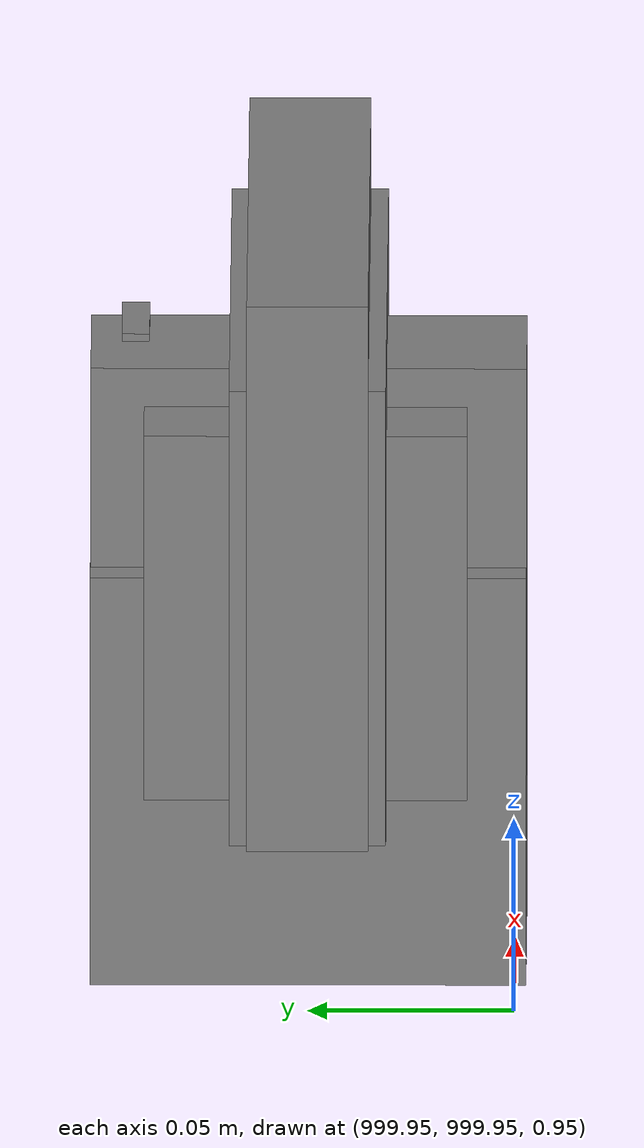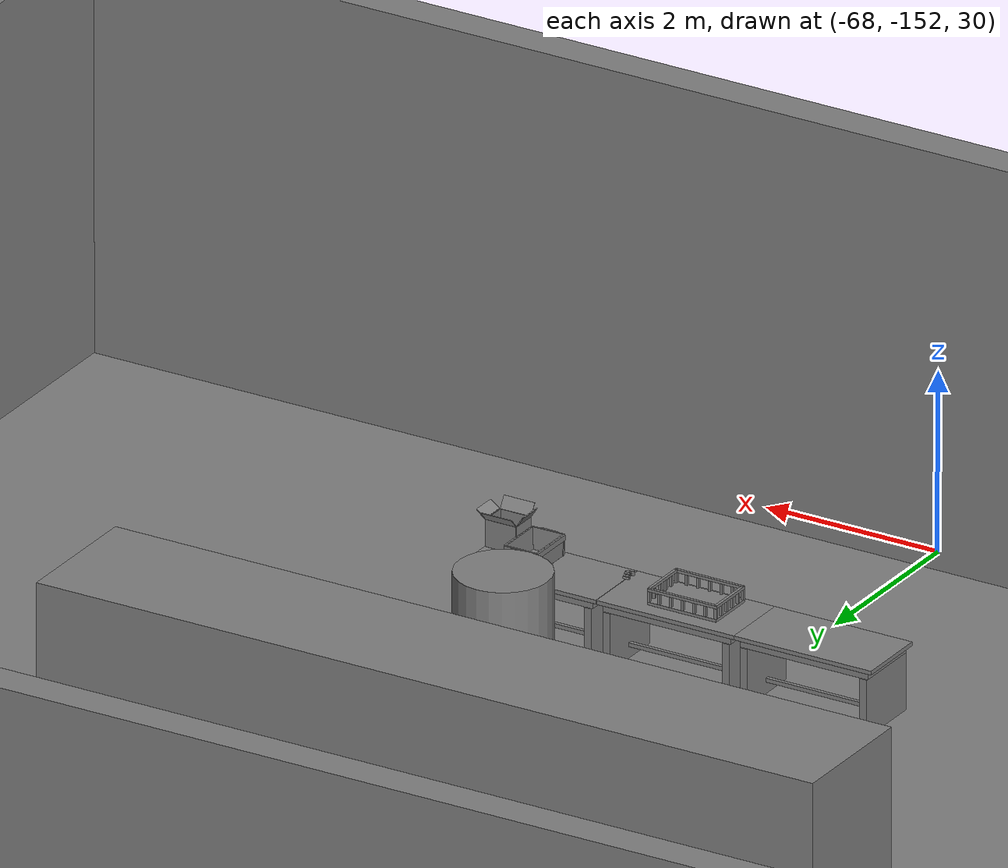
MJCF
<mujoco>
    <option gravity="0.000000000 0.000000000 -9.810000420" timestep="0.0049999999" integrator="implicitfast" density="1.225" viscosity="1.8000001e-05" noslip_iterations="10" iterations="100" sdf_iterations="50">
        <flag multiccd="disable"/>
    </option>
    <size memory="1000M"/>
    <compiler coordinate="local"/>
    <worldbody>
        <light cutoff="30" pos="0 1 1" dir="0 -1 -2"/>
        <light cutoff="30" pos="0 -1 1" dir="0 1 -2"/>
        <body pos="1000.000000000 1000.000000000 1.000000000" euler="0.000000000 0.000000000 180.000000000" name="openloong_gripper_2f85_fix_base_usda_battery_01">
            <geom contype="1" conaffinity="1" density="1000" type="box" material="" rgba="0.500000000 0.500000000 0.500000000 1.000000000" solimp="0.899999976 0.949999988 0.001000000" friction="1.000000000 0.005000000 0.000100000" solref="0.020000000 1.000000000" margin="0" condim="3" group="0" pos="-0.011123657 -0.041940309 0.101691343" quat="1.000000000 0.000000000 0.000000000 0.000000000" size="0.010800000 0.003375000 0.004725000" name="openloong_gripper_2f85_fix_base_usda_geom_2A155641_96BF_44D6_964E_5A612BD5458A"/>
            <geom contype="1" conaffinity="1" density="1000" type="box" material="" rgba="0.500000000 0.500000000 0.500000000 1.000000000" solimp="0.899999976 0.949999988 0.001000000" friction="1.000000000 0.005000000 0.000100000" solref="0.020000000 1.000000000" margin="0" condim="3" group="0" pos="-0.010876465 -0.044247437 0.047066893" quat="0.998702705 -0.050920475 0.000000000 0.000000000" size="0.009450001 0.002700000 0.024975000" name="openloong_gripper_2f85_fix_base_usda_geom_C9D246F2_CB18_4980_9DE7_551F5D63523E"/>
            <geom contype="1" conaffinity="1" density="1000" type="box" material="" rgba="0.500000000 0.500000000 0.500000000 1.000000000" solimp="0.899999976 0.949999988 0.001000000" friction="1.000000000 0.005000000 0.000100000" solref="0.020000000 1.000000000" margin="0" condim="3" group="0" pos="-0.001235962 -0.000659180 0.047381196" quat="1.000000000 0.000000000 0.000000000 0.000000000" size="0.039420001 0.039150000 0.047250003" name="openloong_gripper_2f85_fix_base_usda_geom_617585E5_027D_4602_A8A3_CF0FDA8DBDF7"/>
            <geom contype="1" conaffinity="1" density="1000" type="box" material="" rgba="0.500000000 0.500000000 0.500000000 1.000000000" solimp="0.899999976 0.949999988 0.001000000" friction="1.000000000 0.005000000 0.000100000" solref="0.020000000 1.000000000" margin="0" condim="3" group="0" pos="-0.010876465 -0.039138794 0.009851727" quat="1.000000000 0.000000000 0.000000000 0.000000000" size="0.009450001 0.010800000 0.013500000" name="openloong_gripper_2f85_fix_base_usda_geom_E14D80DB_8DE8_4AED_995E_CD19BEB679FE"/>
            <geom contype="1" conaffinity="1" density="1000" type="box" material="" rgba="0.500000000 0.500000000 0.500000000 1.000000000" solimp="0.899999976 0.949999988 0.001000000" friction="1.000000000 0.005000000 0.000100000" solref="0.020000000 1.000000000" margin="0" condim="3" group="0" pos="-0.010876465 -0.041528322 0.071508206" quat="1.000000000 0.000000000 0.000000000 0.000000000" size="0.009450001 0.002700000 0.027000001" name="openloong_gripper_2f85_fix_base_usda_geom_5FDC9DDA_9045_40DF_979A_0EEC846067D5"/>
            <freejoint name="openloong_gripper_2f85_fix_base_usda_battery_01_joint"/>
            <site size="0.005000000 0.005000000 0.005000000" rgba="0.500000000 0.500000000 0.500000000 1.000000000" pos="0.000000000 0.000000000 0.000000000" quat="0.999961913 0.008726500 0.000000000 0.000000000" group="0" type="sphere" name="openloong_gripper_2f85_fix_base_usda_battery_01site"/>
        </body>
        <body pos="-65.893028259 -149.612487793 31.164037704" euler="-102.706794739 -34.031127930 -36.400146484" mocap="true" name="spotlight6_SpotLight"/>
        <body pos="-65.938949585 -148.953002930 31.165113449" euler="162.312194824 -32.474899292 16.216959000" mocap="true" name="spotlight3_SpotLight"/>
        <body pos="1000.000000000 1000.000000000 1.000000000" euler="0.000000000 0.000000000 180.000000000" name="openloong_gripper_2f85_fix_base_usda_wifi_box">
            <geom contype="1" conaffinity="1" density="1000" type="box" material="" rgba="0.500000000 0.500000000 0.500000000 1.000000000" solimp="0.899999976 0.949999988 0.001000000" friction="1.000000000 0.005000000 0.000100000" solref="0.020000000 1.000000000" margin="0" condim="3" group="0" pos="0.000000000 0.000000000 0.058978677" quat="0.000000000 0.000000047 0.000000000 1.000000000" size="0.068499997 0.018999999 0.059000000" name="openloong_gripper_2f85_fix_base_usda_geom_5F5D571B_82B4_47B3_BBDA_34A905C7F182"/>
            <freejoint name="openloong_gripper_2f85_fix_base_usda_wifi_box_joint"/>
            <site size="0.005000000 0.005000000 0.005000000" rgba="0.500000000 0.500000000 0.500000000 1.000000000" pos="0.000000000 0.000000000 0.000000000" quat="0.999961913 0.008726500 0.000000000 0.000000000" group="0" type="sphere" name="openloong_gripper_2f85_fix_base_usda_wifi_boxsite"/>
        </body>
        <body pos="1000.000000000 1000.000000000 1.000000000" euler="0.000000000 0.000000000 180.000000000" name="openloong_gripper_2f85_fix_base_usda_cpu_fan">
            <geom contype="1" conaffinity="1" density="1000" type="box" material="" rgba="0.500000000 0.500000000 0.500000000 1.000000000" solimp="0.899999976 0.949999988 0.001000000" friction="1.000000000 0.005000000 0.000100000" solref="0.020000000 1.000000000" margin="0" condim="3" group="0" pos="0.000000000 0.000000000 0.070034981" quat="0.000000000 0.000000000 0.000000000 1.000000000" size="0.070700005 0.014699999 0.070700005" name="openloong_gripper_2f85_fix_base_usda_geom_8AF75C06_2BCA_49B3_84E0_1F7652D072E4"/>
            <freejoint name="openloong_gripper_2f85_fix_base_usda_cpu_fan_joint"/>
            <site size="0.005000000 0.005000000 0.005000000" rgba="0.500000000 0.500000000 0.500000000 1.000000000" pos="0.000000000 0.000000000 0.000000000" quat="0.999961913 0.008726535 0.000000000 0.000000000" group="0" type="sphere" name="openloong_gripper_2f85_fix_base_usda_cpu_fancsite"/>
        </body>
        <body pos="1000.000000000 1000.000000000 1.000000000" euler="0.000011953 0.000005123 -179.999984741" name="openloong_gripper_2f85_fix_base_usda_intel_box">
            <geom contype="1" conaffinity="1" density="1000" type="box" material="" rgba="0.500000000 0.500000000 0.500000000 1.000000000" solimp="0.899999976 0.949999988 0.001000000" friction="1.000000000 0.005000000 0.000100000" solref="0.020000000 1.000000000" margin="0" condim="3" group="0" pos="0.000000000 -0.000067139 0.000082284" quat="0.707106709 0.000000225 0.000000253 0.707106650" size="0.052800003 0.025300000 0.052800003" name="openloong_gripper_2f85_fix_base_usda_geom_9EC9D3CB_775E_42EC_8060_A853A3A16E8C"/>
            <freejoint name="openloong_gripper_2f85_fix_base_usda_intel_box_joint"/>
            <site size="0.005000000 0.005000000 0.005000000" rgba="0.500000000 0.500000000 0.500000000 1.000000000" pos="0.000000000 0.000000000 0.000000000" quat="0.999961913 0.008726500 0.000000000 0.000000000" group="0" type="sphere" name="openloong_gripper_2f85_fix_base_usda_intel_boxsite"/>
        </body>
        <body pos="-66.294639587 -149.562072754 31.170972824" euler="138.263442993 47.897010803 89.566810608" mocap="true" name="spotlight5_SpotLight"/>
        <body pos="1000.000000000 999.999938965 1.000000000" euler="0.000000000 0.000000000 180.000000000" name="openloong_gripper_2f85_fix_base_usda_intelcore_i5">
            <geom contype="1" conaffinity="1" density="1000" type="box" material="" rgba="0.500000000 0.500000000 0.500000000 1.000000000" solimp="0.899999976 0.949999988 0.001000000" friction="1.000000000 0.005000000 0.000100000" solref="0.020000000 1.000000000" margin="0" condim="3" group="0" pos="0.000000000 0.000000000 0.051722717" quat="0.707106709 0.000000000 0.000000000 -0.707106769" size="0.052800000 0.018080002 0.052800000" name="openloong_gripper_2f85_fix_base_usda_geom_E940262B_9DFC_4872_8D3D_7AE3B14CDB60"/>
            <freejoint name="openloong_gripper_2f85_fix_base_usda_intelcore_i5_joint"/>
            <site size="0.005000000 0.005000000 0.005000000" rgba="0.500000000 0.500000000 0.500000000 1.000000000" pos="0.000000000 0.000000000 0.000000000" quat="0.999961913 0.008726534 0.000000000 0.000000000" group="0" type="sphere" name="openloong_gripper_2f85_fix_base_usda_intelcore_i5site"/>
        </body>
        <body pos="-64.866622925 -149.383972168 30.183746338" euler="89.999984741 89.999946594 0.000000000" name="openloong_gripper_2f85_fix_base_usda_bluebox_01">
            <geom contype="1" conaffinity="1" density="1000" type="box" material="" rgba="0.500000000 0.500000000 0.500000000 1.000000000" solimp="0.899999976 0.949999988 0.001000000" friction="1.000000000 0.005000000 0.000100000" solref="0.020000000 1.000000000" margin="0" condim="3" group="0" pos="0.276580811 0.187225342 0.000068665" quat="0.707106948 0.000077471 0.707106352 0.000077486" size="0.100000001 0.057999998 0.010000000" name="openloong_gripper_2f85_fix_base_usda_geom_DED9DF66_7FF4_49FB_9ECF_3BAD7C8453B8"/>
            <geom contype="1" conaffinity="1" density="1000" type="box" material="" rgba="0.500000000 0.500000000 0.500000000 1.000000000" solimp="0.899999976 0.949999988 0.001000000" friction="1.000000000 0.005000000 0.000100000" solref="0.020000000 1.000000000" margin="0" condim="3" group="0" pos="0.000000000 0.002883911 0.000000000" quat="0.999999881 0.000000000 0.000000000 0.000000000" size="0.254000008 0.003000000 0.172000006" name="openloong_gripper_2f85_fix_base_usda_geom_953836AD_D6F4_48A7_94B5_54FFB738AD34"/>
            <geom contype="1" conaffinity="1" density="1000" type="box" material="" rgba="0.500000000 0.500000000 0.500000000 1.000000000" solimp="0.899999976 0.949999988 0.001000000" friction="1.000000000 0.005000000 0.000100000" solref="0.020000000 1.000000000" margin="0" condim="3" group="0" pos="0.000000000 0.124874115 0.173484802" quat="0.999796331 0.020176515 -0.000000015 0.000000030" size="0.259999990 0.119999997 0.007000000" name="openloong_gripper_2f85_fix_base_usda_geom_43581D79_D882_4034_AB12_7820A7ECC740"/>
            <geom contype="1" conaffinity="1" density="1000" type="box" material="" rgba="0.500000000 0.500000000 0.500000000 1.000000000" solimp="0.899999976 0.949999988 0.001000000" friction="1.000000000 0.005000000 0.000100000" solref="0.020000000 1.000000000" margin="0" condim="3" group="0" pos="0.000000000 0.124874115 -0.173469543" quat="0.999796331 -0.020176545 -0.000000015 0.000000000" size="0.259999990 0.119999997 0.007000000" name="openloong_gripper_2f85_fix_base_usda_geom_D7724C45_B61A_494F_AD9D_71A4FBE475CC"/>
            <geom contype="1" conaffinity="1" density="1000" type="box" material="" rgba="0.500000000 0.500000000 0.500000000 1.000000000" solimp="0.899999976 0.949999988 0.001000000" friction="1.000000000 0.005000000 0.000100000" solref="0.020000000 1.000000000" margin="0" condim="3" group="0" pos="0.000000000 0.214008331 0.188980103" quat="0.999912977 0.013176724 0.000000015 0.000000000" size="0.259999990 0.029999999 0.012500000" name="openloong_gripper_2f85_fix_base_usda_geom_76523838_CBE8_49E7_BC1C_2467590450BF"/>
            <geom contype="1" conaffinity="1" density="1000" type="box" material="" rgba="0.500000000 0.500000000 0.500000000 1.000000000" solimp="0.899999976 0.949999988 0.001000000" friction="1.000000000 0.005000000 0.000100000" solref="0.020000000 1.000000000" margin="0" condim="3" group="0" pos="-0.258361816 0.125289917 0.001876831" quat="0.702796936 -0.020792112 0.710783124 0.020769298" size="0.189999998 0.119999997 0.009000000" name="openloong_gripper_2f85_fix_base_usda_geom_D92EE89F_64AE_4673_B7E4_771E5BE5806C"/>
            <geom contype="1" conaffinity="1" density="1000" type="box" material="" rgba="0.500000000 0.500000000 0.500000000 1.000000000" solimp="0.899999976 0.949999988 0.001000000" friction="1.000000000 0.005000000 0.000100000" solref="0.020000000 1.000000000" margin="0" condim="3" group="0" pos="0.000000000 0.214008331 -0.188980103" quat="0.999912977 -0.013176769 0.000000030 0.000000015" size="0.259999990 0.029999999 0.012500000" name="openloong_gripper_2f85_fix_base_usda_geom_27605056_2F82_4BA1_916A_102768F305EC"/>
            <geom contype="1" conaffinity="1" density="1000" type="box" material="" rgba="0.500000000 0.500000000 0.500000000 1.000000000" solimp="0.899999976 0.949999988 0.001000000" friction="1.000000000 0.005000000 0.000100000" solref="0.020000000 1.000000000" margin="0" condim="3" group="0" pos="-0.276611328 0.187225342 0.000068665" quat="0.707106650 0.000077441 0.707106709 0.000077456" size="0.100000001 0.057999998 0.010000000" name="openloong_gripper_2f85_fix_base_usda_geom_E5325284_6DEB_4790_968F_F117D303631D"/>
            <geom contype="1" conaffinity="1" density="1000" type="box" material="" rgba="0.500000000 0.500000000 0.500000000 1.000000000" solimp="0.899999976 0.949999988 0.001000000" friction="1.000000000 0.005000000 0.000100000" solref="0.020000000 1.000000000" margin="0" condim="3" group="0" pos="0.258331299 0.125289917 0.001876831" quat="0.702851415 0.018856421 0.710823774 -0.019329369" size="0.189999998 0.119999997 0.009000000" name="openloong_gripper_2f85_fix_base_usda_geom_2779B938_BF01_4B6F_99A2_102BB0AD7201"/>
            <freejoint name="openloong_gripper_2f85_fix_base_usda_bluebox_01_joint"/>
            <site size="0.005000000 0.005000000 0.005000000" rgba="0.500000000 0.500000000 0.500000000 1.000000000" pos="0.000000000 0.000000000 0.000000000" quat="0.999961913 0.008726534 0.000000000 0.000000000" group="0" type="sphere" name="openloong_gripper_2f85_fix_base_usda_bluebox_01site"/>
        </body>
        <body pos="-64.496299744 -149.491867065 30.235729218" euler="0.000000000 0.000000000 89.999946594" name="openloong_gripper_2f85_fix_base_usda_cardboardbox_01">
            <geom contype="1" conaffinity="1" density="1000" type="box" material="" rgba="0.500000000 0.500000000 0.500000000 1.000000000" solimp="0.899999976 0.949999988 0.001000000" friction="1.000000000 0.005000000 0.000100000" solref="0.020000000 1.000000000" margin="0" condim="3" group="0" pos="-0.003166199 -0.004086494 0.005052090" quat="1.000000000 0.000000000 0.000000000 0.000000000" size="0.142499998 0.177500010 0.005000000" name="openloong_gripper_2f85_fix_base_usda_geom_9DA26044_5EF3_4858_906E_89B5111D9AD6"/>
            <geom contype="1" conaffinity="1" density="1000" type="box" material="" rgba="0.500000000 0.500000000 0.500000000 1.000000000" solimp="0.899999976 0.949999988 0.001000000" friction="1.000000000 0.005000000 0.000100000" solref="0.020000000 1.000000000" margin="0" condim="3" group="0" pos="-0.003166199 0.170316696 0.150570869" quat="1.000000000 0.000000000 0.000000000 0.000000000" size="0.142499998 0.005000000 0.149999991" name="openloong_gripper_2f85_fix_base_usda_geom_1B05C619_D43E_4E39_AD24_C4799012FBA0"/>
            <geom contype="1" conaffinity="1" density="1000" type="box" material="" rgba="0.500000000 0.500000000 0.500000000 1.000000000" solimp="0.899999976 0.949999988 0.001000000" friction="1.000000000 0.005000000 0.000100000" solref="0.020000000 1.000000000" margin="0" condim="3" group="0" pos="-0.147399902 -0.005307198 0.150570869" quat="1.000000000 0.000000000 0.000000000 0.000000000" size="0.005000000 0.177500010 0.149999991" name="openloong_gripper_2f85_fix_base_usda_geom_A6597E00_04AB_4C16_AE1F_2B50CA36F0C0"/>
            <geom contype="1" conaffinity="1" density="1000" type="box" material="" rgba="0.500000000 0.500000000 0.500000000 1.000000000" solimp="0.899999976 0.949999988 0.001000000" friction="1.000000000 0.005000000 0.000100000" solref="0.020000000 1.000000000" margin="0" condim="3" group="0" pos="0.140275955 -0.005307198 0.150570869" quat="1.000000000 0.000000000 0.000000000 0.000000000" size="0.005000000 0.177500010 0.149999991" name="openloong_gripper_2f85_fix_base_usda_geom_E6A986EB_0FAB_4082_B816_1B8B9EA46325"/>
            <geom contype="1" conaffinity="1" density="1000" type="box" material="" rgba="0.500000000 0.500000000 0.500000000 1.000000000" solimp="0.899999976 0.949999988 0.001000000" friction="1.000000000 0.005000000 0.000100000" solref="0.020000000 1.000000000" margin="0" condim="3" group="0" pos="-0.003166199 -0.181550980 0.150570869" quat="1.000000000 0.000000000 0.000000000 0.000000000" size="0.142499998 0.005000000 0.149999991" name="openloong_gripper_2f85_fix_base_usda_geom_752E6767_5FA0_4F00_869A_C63BDE0EFCFC"/>
            <freejoint name="openloong_gripper_2f85_fix_base_usda_cardboardbox_01_joint"/>
            <site size="0.005000000 0.005000000 0.005000000" rgba="0.500000000 0.500000000 0.500000000 1.000000000" pos="0.000000000 0.000000000 0.000000000" quat="0.999961913 0.008726535 0.000000000 0.000000000" group="0" type="sphere" name="openloong_gripper_2f85_fix_base_usda_site_28BFEC7D_E7BA_4CA5_8C41_2C8CC561886E"/>
            <body pos="0.139160156 -0.004048347 0.301930904" euler="-179.999954224 49.383502960 179.999954224" name="openloong_gripper_2f85_fix_base_usda_A1_006">
                <geom contype="1" conaffinity="1" density="1000" type="box" material="" rgba="0.500000000 0.500000000 0.500000000 1.000000000" solimp="0.899999976 0.949999988 0.001000000" friction="1.000000000 0.005000000 0.000100000" solref="0.020000000 1.000000000" margin="0" condim="3" group="0" pos="-0.071587563 0.000009537 0.001745224" quat="0.999999881 0.000000000 0.000000000 0.000000000" size="0.071249999 0.179999992 0.002500000" name="openloong_gripper_2f85_fix_base_usda_geom_B824E65A_0504_4679_88EE_0DD17602EFB6"/>
                <joint armature="0" stiffness="0.07" damping="0.0099999998" axis="0.000000 1.000000 0.000000" type="hinge" name="openloong_gripper_2f85_fix_base_usda_A1_006"/>
            </body>
            <body pos="-0.145902634 -0.004086494 0.301938057" euler="-180.000000000 -60.000011444 -180.000000000" name="openloong_gripper_2f85_fix_base_usda_A2_006">
                <geom contype="1" conaffinity="1" density="1000" type="box" material="" rgba="0.500000000 0.500000000 0.500000000 1.000000000" solimp="0.899999976 0.949999988 0.001000000" friction="1.000000000 0.005000000 0.000100000" solref="0.020000000 1.000000000" margin="0" condim="3" group="0" pos="0.071268082 0.000009537 0.002717972" quat="0.000002921 0.000000000 -0.000000030 0.999999881" size="0.071249999 0.179999992 0.002500000" name="openloong_gripper_2f85_fix_base_usda_geom_73287CA4_A652_4B9A_AE38_0FE43847F69A"/>
                <joint armature="0" stiffness="0.07" damping="0.0099999998" axis="0.000000 1.000000 0.000000" type="hinge" name="openloong_gripper_2f85_fix_base_usda_A2_006"/>
            </body>
            <body pos="-0.003385544 0.175991058 0.301930904" euler="-125.858116150 -0.000004561 0.000002331" name="openloong_gripper_2f85_fix_base_usda_B2_006">
                <geom contype="1" conaffinity="1" density="1000" type="box" material="" rgba="0.500000000 0.500000000 0.500000000 1.000000000" solimp="0.899999976 0.949999988 0.001000000" friction="1.000000000 0.005000000 0.000100000" solref="0.020000000 1.000000000" margin="0" condim="3" group="0" pos="0.000009537 -0.070939064 -0.002470016" quat="0.999614120 0.027776197 -0.000000015 0.000000030" size="0.137500003 0.064999998 0.005000000" name="openloong_gripper_2f85_fix_base_usda_geom_F57FE2A8_095E_4BD5_8F56_8FAB36DDA3ED"/>
                <joint armature="0" stiffness="0.07" damping="0.0099999998" axis="1.000000 0.000000 0.000000" type="hinge" name="openloong_gripper_2f85_fix_base_usda_B2_006"/>
            </body>
            <body pos="-0.003385544 -0.184140205 0.301938057" euler="147.805557251 0.000000000 0.000000000" name="openloong_gripper_2f85_fix_base_usda_B1_006">
                <geom contype="1" conaffinity="1" density="1000" type="box" material="" rgba="0.500000000 0.500000000 0.500000000 1.000000000" solimp="0.899999976 0.949999988 0.001000000" friction="1.000000000 0.005000000 0.000100000" solref="0.020000000 1.000000000" margin="0" condim="3" group="0" pos="-0.000028610 0.070202351 -0.002703667" quat="0.999614179 -0.027776167 0.000000000 0.000000000" size="0.137500003 0.064999998 0.005000000" name="openloong_gripper_2f85_fix_base_usda_geom_A4D9F644_27C0_45F7_B48D_BB77F0F52049"/>
                <joint armature="0" stiffness="0.07" damping="0.0099999998" axis="1.000000 0.000000 0.000000" type="hinge" name="openloong_gripper_2f85_fix_base_usda_B1_006"/>
            </body>
        </body>
        <body pos="-65.882858276 -149.481979370 30.229999542" euler="-64.487716675 0.000000000 0.000000000" name="openloong_gripper_2f85_fix_base_usda_Barcode">
            <geom contype="1" conaffinity="1" density="1000" type="box" material="" rgba="0.500000000 0.500000000 0.500000000 1.000000000" solimp="0.899999976 0.949999988 0.001000000" friction="1.000000000 0.005000000 0.000100000" solref="0.020000000 1.000000000" margin="0" condim="3" group="0" pos="0.000000000 0.013038635 0.001419067" quat="0.000000000 0.000000000 0.000000000 1.000000119" size="0.034000002 0.010000000 0.017999999" name="openloong_gripper_2f85_fix_base_usda_geom_304CBCA8_A2F9_42FC_8DEB_284EED121709"/>
            <geom contype="1" conaffinity="1" density="1000" type="box" material="" rgba="0.500000000 0.500000000 0.500000000 1.000000000" solimp="0.899999976 0.949999988 0.001000000" friction="1.000000000 0.005000000 0.000100000" solref="0.020000000 1.000000000" margin="0" condim="3" group="0" pos="0.000000000 -0.035301208 -0.007095337" quat="0.000000000 0.000000000 -0.043619365 0.999048233" size="0.028999999 0.010000000 0.020000000" name="openloong_gripper_2f85_fix_base_usda_geom_0FB101CA_EA34_4BDF_A95C_0A36BF41DF14"/>
            <geom contype="1" conaffinity="1" density="1000" type="box" material="" rgba="0.500000000 0.500000000 0.500000000 1.000000000" solimp="0.899999976 0.949999988 0.001000000" friction="1.000000000 0.005000000 0.000100000" solref="0.020000000 1.000000000" margin="0" condim="3" group="0" pos="0.000000000 -0.043411255 -0.011749268" quat="0.922262907 0.386563420 0.000000000 0.000000000" size="0.026000001 0.010000000 0.020000000" name="openloong_gripper_2f85_fix_base_usda_geom_6424C45F_D2A9_47D8_AE68_76A127945FC3"/>
            <geom contype="1" conaffinity="1" density="1000" type="box" material="" rgba="0.500000000 0.500000000 0.500000000 1.000000000" solimp="0.899999976 0.949999988 0.001000000" friction="1.000000000 0.005000000 0.000100000" solref="0.020000000 1.000000000" margin="0" condim="3" group="0" pos="0.000000000 -0.016967773 -0.031860352" quat="0.000000000 0.000000000 0.000000000 1.000000119" size="0.008000000 0.010000000 0.013000000" name="openloong_gripper_2f85_fix_base_usda_geom_29C96044_3978_4CEE_9631_806320CDDDF5"/>
            <geom contype="1" conaffinity="1" density="1000" type="box" material="" rgba="0.500000000 0.500000000 0.500000000 1.000000000" solimp="0.899999976 0.949999988 0.001000000" friction="1.000000000 0.005000000 0.000100000" solref="0.020000000 1.000000000" margin="0" condim="3" group="0" pos="0.000000000 -0.001869202 0.000312805" quat="0.953716993 0.300705761 0.000000000 0.000000000" size="0.032000002 0.010000000 0.018999999" name="openloong_gripper_2f85_fix_base_usda_geom_767A03EC_1A19_4296_A694_3456B786D966"/>
            <geom contype="1" conaffinity="1" density="1000" type="box" material="" rgba="0.500000000 0.500000000 0.500000000 1.000000000" solimp="0.899999976 0.949999988 0.001000000" friction="1.000000000 0.005000000 0.000100000" solref="0.020000000 1.000000000" margin="0" condim="3" group="0" pos="0.000000000 -0.019531250 -0.003173828" quat="0.953716993 0.300705761 0.000000000 0.000000000" size="0.030999999 0.010000000 0.020000000" name="openloong_gripper_2f85_fix_base_usda_geom_9212C331_2559_4255_B86F_88B17A683860"/>
            <geom contype="1" conaffinity="1" density="1000" type="box" material="" rgba="0.500000000 0.500000000 0.500000000 1.000000000" solimp="0.899999976 0.949999988 0.001000000" friction="1.000000000 0.005000000 0.000100000" solref="0.020000000 1.000000000" margin="0" condim="3" group="0" pos="0.000000000 -0.035301208 -0.007095337" quat="0.953716993 0.300705761 0.000000000 0.000000000" size="0.028999999 0.010000000 0.020000000" name="openloong_gripper_2f85_fix_base_usda_geom_67CAFA79_3037_4652_9420_28F06A8F213A"/>
            <geom contype="1" conaffinity="1" density="1000" type="box" material="" rgba="0.500000000 0.500000000 0.500000000 1.000000000" solimp="0.899999976 0.949999988 0.001000000" friction="1.000000000 0.005000000 0.000100000" solref="0.020000000 1.000000000" margin="0" condim="3" group="0" pos="0.000000000 -0.042617798 -0.071121216" quat="0.000000000 0.000000000 0.000000000 1.000000119" size="0.013000000 0.021000000 0.059999999" name="openloong_gripper_2f85_fix_base_usda_geom_AE3D8646_ECA4_4783_905C_9D1B34693C63"/>
            <freejoint name="openloong_gripper_2f85_fix_base_usda_Barcode_joint"/>
            <site size="0.005000000 0.005000000 0.005000000" rgba="0.500000000 0.500000000 0.500000000 1.000000000" pos="0.000000000 0.000000000 0.000000000" quat="1.000000000 0.000000000 0.000000000 0.000000000" group="0" type="sphere" name="openloong_gripper_2f85_fix_base_usda_Barcode_site"/>
        </body>
        <body pos="-66.745018005 -149.392349243 30.184000015" euler="0.000000000 0.000000000 89.999946594" name="[22330365496465]_Basket_01">
            <geom contype="1" conaffinity="1" density="1000" type="box" material="" rgba="0.500000000 0.500000000 0.500000000 1.000000000" solimp="0.899999976 0.949999988 0.001000000" friction="1.000000000 0.005000000 0.000100000" solref="0.020000000 1.000000000" margin="0" condim="3" group="0" pos="-0.052425385 0.389207840 0.089787483" quat="0.707107008 0.000000000 0.000000000 0.707106411" size="0.014249999 0.014249999 0.059999999" name="[22330365496465]_geom_8A28F94C_379D_4EAF_9BEC_058F972B4048"/>
            <geom contype="1" conaffinity="1" density="1000" type="box" material="" rgba="0.500000000 0.500000000 0.500000000 1.000000000" solimp="0.899999976 0.949999988 0.001000000" friction="1.000000000 0.005000000 0.000100000" solref="0.020000000 1.000000000" margin="0" condim="3" group="0" pos="0.264015198 -0.133043289 0.089787483" quat="0.707107008 0.000000000 0.000000000 0.707106411" size="0.014249999 0.014249999 0.059999999" name="[22330365496465]_geom_B42885B2_A8D6_4543_9E66_DD4BA861AC30"/>
            <geom contype="1" conaffinity="1" density="1000" type="box" material="" rgba="0.500000000 0.500000000 0.500000000 1.000000000" solimp="0.899999976 0.949999988 0.001000000" friction="1.000000000 0.005000000 0.000100000" solref="0.020000000 1.000000000" margin="0" condim="3" group="0" pos="-0.264015198 -0.265548706 0.089793205" quat="0.707107008 0.000000000 0.000000000 0.707106411" size="0.014249999 0.014249999 0.059999999" name="[22330365496465]_geom_1196395F_2477_48ED_B902_AF45F0B2C65D"/>
            <geom contype="1" conaffinity="1" density="1000" type="box" material="" rgba="0.500000000 0.500000000 0.500000000 1.000000000" solimp="0.899999976 0.949999988 0.001000000" friction="1.000000000 0.005000000 0.000100000" solref="0.020000000 1.000000000" margin="0" condim="3" group="0" pos="-0.160263062 -0.389322281 0.089793205" quat="0.707107008 0.000000000 0.000000000 0.707106411" size="0.014249999 0.014249999 0.059999999" name="[22330365496465]_geom_D58ACE50_51DC_495C_94CC_01722B89D7FE"/>
            <geom contype="1" conaffinity="1" density="1000" type="box" material="" rgba="0.500000000 0.500000000 0.500000000 1.000000000" solimp="0.899999976 0.949999988 0.001000000" friction="1.000000000 0.005000000 0.000100000" solref="0.020000000 1.000000000" margin="0" condim="3" group="0" pos="0.162265778 -0.389322281 0.089787483" quat="0.707107008 0.000000000 0.000000000 0.707106411" size="0.014249999 0.014249999 0.059999999" name="[22330365496465]_geom_FFD4BAAF_278D_4928_8788_79E6465E1984"/>
            <geom contype="1" conaffinity="1" density="1000" type="box" material="" rgba="0.500000000 0.500000000 0.500000000 1.000000000" solimp="0.899999976 0.949999988 0.001000000" friction="1.000000000 0.005000000 0.000100000" solref="0.020000000 1.000000000" margin="0" condim="3" group="0" pos="0.264015198 0.389207840 0.089787483" quat="0.707107008 0.000000000 0.000000000 0.707106411" size="0.014249999 0.014249999 0.059999999" name="[22330365496465]_geom_1E147407_8F50_43C1_97CC_C004AC42EA33"/>
            <geom contype="1" conaffinity="1" density="1000" type="box" material="" rgba="0.500000000 0.500000000 0.500000000 1.000000000" solimp="0.899999976 0.949999988 0.001000000" friction="1.000000000 0.005000000 0.000100000" solref="0.020000000 1.000000000" margin="0" condim="3" group="0" pos="-0.264015198 -0.133043289 0.089793205" quat="0.707107008 0.000000000 0.000000000 0.707106411" size="0.014249999 0.014249999 0.059999999" name="[22330365496465]_geom_8666725F_B7F0_4648_8066_52DB9F434AC7"/>
            <geom contype="1" conaffinity="1" density="1000" type="box" material="" rgba="0.500000000 0.500000000 0.500000000 1.000000000" solimp="0.899999976 0.949999988 0.001000000" friction="1.000000000 0.005000000 0.000100000" solref="0.020000000 1.000000000" margin="0" condim="3" group="0" pos="-0.264026642 0.269256592 0.089793205" quat="0.707107008 0.000000000 0.000000000 0.707106411" size="0.014249999 0.014249999 0.059999999" name="[22330365496465]_geom_4C6D0064_1CC4_4D88_8FC5_327A1EF3CC31"/>
            <geom contype="1" conaffinity="1" density="1000" type="box" material="" rgba="0.500000000 0.500000000 0.500000000 1.000000000" solimp="0.899999976 0.949999988 0.001000000" friction="1.000000000 0.005000000 0.000100000" solref="0.020000000 1.000000000" margin="0" condim="3" group="0" pos="0.054462433 0.389207840 0.089787483" quat="0.707107008 0.000000000 0.000000000 0.707106411" size="0.014249999 0.014249999 0.059999999" name="[22330365496465]_geom_BA431E29_3F03_4EC2_B4B3_166948A8FBF4"/>
            <geom contype="1" conaffinity="1" density="1000" type="box" material="" rgba="0.500000000 0.500000000 0.500000000 1.000000000" solimp="0.899999976 0.949999988 0.001000000" friction="1.000000000 0.005000000 0.000100000" solref="0.020000000 1.000000000" margin="0" condim="3" group="0" pos="0.054462433 -0.389322281 0.089787483" quat="0.707107008 0.000000000 0.000000000 0.707106411" size="0.014249999 0.014249999 0.059999999" name="[22330365496465]_geom_6AA1AFFB_8551_4959_A337_C6D7E494A7E7"/>
            <geom contype="1" conaffinity="1" density="1000" type="box" material="" rgba="0.500000000 0.500000000 0.500000000 1.000000000" solimp="0.899999976 0.949999988 0.001000000" friction="1.000000000 0.005000000 0.000100000" solref="0.020000000 1.000000000" margin="0" condim="3" group="0" pos="0.264015198 0.269256592 0.089793205" quat="0.707107008 0.000000000 0.000000000 0.707106411" size="0.014249999 0.014249999 0.059999999" name="[22330365496465]_geom_8E540B97_581D_4EAB_A69E_16AA89EDD3C7"/>
            <geom contype="1" conaffinity="1" density="1000" type="box" material="" rgba="0.500000000 0.500000000 0.500000000 1.000000000" solimp="0.899999976 0.949999988 0.001000000" friction="1.000000000 0.005000000 0.000100000" solref="0.020000000 1.000000000" margin="0" condim="3" group="0" pos="0.264015198 -0.389322281 0.089787483" quat="0.707107008 0.000000000 0.000000000 0.707106411" size="0.014249999 0.014249999 0.059999999" name="[22330365496465]_geom_10A54313_A321_48B8_A747_7CF6B4B24A65"/>
            <geom contype="1" conaffinity="1" density="1000" type="box" material="" rgba="0.500000000 0.500000000 0.500000000 1.000000000" solimp="0.899999976 0.949999988 0.001000000" friction="1.000000000 0.005000000 0.000100000" solref="0.020000000 1.000000000" margin="0" condim="3" group="0" pos="0.000000000 0.000000000 0.015998840" quat="0.707107008 0.000000000 0.000000000 0.707106411" size="0.403499991 0.279000014 0.015750000" name="[22330365496465]_geom_DE6F391C_7C31_42A1_811C_8CC92E2342F2"/>
            <geom contype="1" conaffinity="1" density="1000" type="box" material="" rgba="0.500000000 0.500000000 0.500000000 1.000000000" solimp="0.899999976 0.949999988 0.001000000" friction="1.000000000 0.005000000 0.000100000" solref="0.020000000 1.000000000" margin="0" condim="3" group="0" pos="0.000000000 -0.389476776 0.163619041" quat="0.707107008 0.000000000 0.000000000 0.707106411" size="0.015000000 0.277500004 0.015750000" name="[22330365496465]_geom_74FEFD5E_3731_431E_AA0C_8765C715BDAB"/>
            <geom contype="1" conaffinity="1" density="1000" type="box" material="" rgba="0.500000000 0.500000000 0.500000000 1.000000000" solimp="0.899999976 0.949999988 0.001000000" friction="1.000000000 0.005000000 0.000100000" solref="0.020000000 1.000000000" margin="0" condim="3" group="0" pos="0.162265778 0.389207840 0.089787483" quat="0.707107008 0.000000000 0.000000000 0.707106411" size="0.014249999 0.014249999 0.059999999" name="[22330365496465]_geom_2E0A8689_A84B_482A_8461_420A2AC963FD"/>
            <geom contype="1" conaffinity="1" density="1000" type="box" material="" rgba="0.500000000 0.500000000 0.500000000 1.000000000" solimp="0.899999976 0.949999988 0.001000000" friction="1.000000000 0.005000000 0.000100000" solref="0.020000000 1.000000000" margin="0" condim="3" group="0" pos="0.000000000 0.389471054 0.163619041" quat="0.707107008 0.000000000 0.000000000 0.707106411" size="0.015000000 0.277500004 0.015750000" name="[22330365496465]_geom_9EEA6FF2_97E6_4A6A_8D8D_131D1F28BD84"/>
            <geom contype="1" conaffinity="1" density="1000" type="box" material="" rgba="0.500000000 0.500000000 0.500000000 1.000000000" solimp="0.899999976 0.949999988 0.001000000" friction="1.000000000 0.005000000 0.000100000" solref="0.020000000 1.000000000" margin="0" condim="3" group="0" pos="-0.263511658 0.000000000 0.163619041" quat="0.707107008 0.000000000 0.000000000 0.707106411" size="0.403499991 0.015000000 0.015750000" name="[22330365496465]_geom_90F02AFB_7691_473A_AEB4_AD2424CBF033"/>
            <geom contype="1" conaffinity="1" density="1000" type="box" material="" rgba="0.500000000 0.500000000 0.500000000 1.000000000" solimp="0.899999976 0.949999988 0.001000000" friction="1.000000000 0.005000000 0.000100000" solref="0.020000000 1.000000000" margin="0" condim="3" group="0" pos="-0.264015198 0.141334534 0.089793205" quat="0.707107008 0.000000000 0.000000000 0.707106411" size="0.014249999 0.014249999 0.059999999" name="[22330365496465]_geom_2AC11ED7_CC96_45C1_8E55_928F5E7258B8"/>
            <geom contype="1" conaffinity="1" density="1000" type="box" material="" rgba="0.500000000 0.500000000 0.500000000 1.000000000" solimp="0.899999976 0.949999988 0.001000000" friction="1.000000000 0.005000000 0.000100000" solref="0.020000000 1.000000000" margin="0" condim="3" group="0" pos="0.264015198 -0.265548706 0.089787483" quat="0.707107008 0.000000000 0.000000000 0.707106411" size="0.014249999 0.014249999 0.059999999" name="[22330365496465]_geom_785EF2DB_30A8_430A_AA2C_76DE257A0786"/>
            <geom contype="1" conaffinity="1" density="1000" type="box" material="" rgba="0.500000000 0.500000000 0.500000000 1.000000000" solimp="0.899999976 0.949999988 0.001000000" friction="1.000000000 0.005000000 0.000100000" solref="0.020000000 1.000000000" margin="0" condim="3" group="0" pos="-0.160263062 0.389207840 0.089787483" quat="0.707107008 0.000000000 0.000000000 0.707106411" size="0.014249999 0.014249999 0.059999999" name="[22330365496465]_geom_F15AF248_ECE6_4206_8EE5_8A18EBC014B4"/>
            <geom contype="1" conaffinity="1" density="1000" type="box" material="" rgba="0.500000000 0.500000000 0.500000000 1.000000000" solimp="0.899999976 0.949999988 0.001000000" friction="1.000000000 0.005000000 0.000100000" solref="0.020000000 1.000000000" margin="0" condim="3" group="0" pos="-0.052425385 -0.389322281 0.089787483" quat="0.707107008 0.000000000 0.000000000 0.707106411" size="0.014249999 0.014249999 0.059999999" name="[22330365496465]_geom_7DE408F4_69A3_475D_BCB4_8EF5A7869AFB"/>
            <geom contype="1" conaffinity="1" density="1000" type="box" material="" rgba="0.500000000 0.500000000 0.500000000 1.000000000" solimp="0.899999976 0.949999988 0.001000000" friction="1.000000000 0.005000000 0.000100000" solref="0.020000000 1.000000000" margin="0" condim="3" group="0" pos="-0.264026642 -0.389322281 0.089793205" quat="0.707107008 0.000000000 0.000000000 0.707106411" size="0.014249999 0.014249999 0.059999999" name="[22330365496465]_geom_D2AF8C35_79B0_4614_B0C9_FABEAAA684A1"/>
            <geom contype="1" conaffinity="1" density="1000" type="box" material="" rgba="0.500000000 0.500000000 0.500000000 1.000000000" solimp="0.899999976 0.949999988 0.001000000" friction="1.000000000 0.005000000 0.000100000" solref="0.020000000 1.000000000" margin="0" condim="3" group="0" pos="0.264015198 0.141334534 0.089787483" quat="0.707107008 0.000000000 0.000000000 0.707106411" size="0.014249999 0.014249999 0.059999999" name="[22330365496465]_geom_7063D9F2_A64C_47DB_A4CB_546732ECF99F"/>
            <geom contype="1" conaffinity="1" density="1000" type="box" material="" rgba="0.500000000 0.500000000 0.500000000 1.000000000" solimp="0.899999976 0.949999988 0.001000000" friction="1.000000000 0.005000000 0.000100000" solref="0.020000000 1.000000000" margin="0" condim="3" group="0" pos="-0.264015198 0.389207840 0.089793205" quat="0.707107008 0.000000000 0.000000000 0.707106411" size="0.014249999 0.014249999 0.059999999" name="[22330365496465]_geom_3ECB137C_4957_41A1_BEDA_EFCE2301B99B"/>
            <geom contype="1" conaffinity="1" density="1000" type="box" material="" rgba="0.500000000 0.500000000 0.500000000 1.000000000" solimp="0.899999976 0.949999988 0.001000000" friction="1.000000000 0.005000000 0.000100000" solref="0.020000000 1.000000000" margin="0" condim="3" group="0" pos="0.264015198 0.004480362 0.089787483" quat="0.707107008 0.000000000 0.000000000 0.707106411" size="0.014249999 0.014249999 0.059999999" name="[22330365496465]_geom_1E16A1B6_782E_42A4_BA85_F418ADBAB175"/>
            <geom contype="1" conaffinity="1" density="1000" type="box" material="" rgba="0.500000000 0.500000000 0.500000000 1.000000000" solimp="0.899999976 0.949999988 0.001000000" friction="1.000000000 0.005000000 0.000100000" solref="0.020000000 1.000000000" margin="0" condim="3" group="0" pos="0.263694763 -0.000011444 0.163619041" quat="0.707107008 0.000000000 0.000000000 0.707106411" size="0.403499991 0.015000000 0.015750000" name="[22330365496465]_geom_AFA46C29_0219_48D6_AFE2_A0EA8EE4E62C"/>
            <geom contype="1" conaffinity="1" density="1000" type="box" material="" rgba="0.500000000 0.500000000 0.500000000 1.000000000" solimp="0.899999976 0.949999988 0.001000000" friction="1.000000000 0.005000000 0.000100000" solref="0.020000000 1.000000000" margin="0" condim="3" group="0" pos="-0.264015198 0.004480362 0.089793205" quat="0.707107008 0.000000000 0.000000000 0.707106411" size="0.014249999 0.014249999 0.059999999" name="[22330365496465]_geom_12776D5E_5115_450C_8221_658C7A05902B"/>
            <freejoint name="[22330365496465]_joint_B9DA98A5_F8F3_4180_903A_46D5A3DE6095"/>
        </body>
        <body pos="0.000000000 0.000000000 0.000000000" euler="0.000000000 0.000000000 0.000000000" name="Static Objects_Static Objects">
            <geom contype="1" conaffinity="1" density="1000" type="box" material="" rgba="0.500000000 0.500000000 0.500000000 1.000000000" solimp="0.899999976 0.949999988 0.001000000" friction="1.000000000 0.005000000 0.000100000" solref="0.020000000 1.000000000" margin="0" condim="3" group="0" pos="-67.544113159 -149.365814209 29.727830887" quat="0.500000417 0.499999970 0.499999553 0.499999970" size="0.381000012 0.319999993 0.041000001" name="Static Objects_geom_26BC1353_6B3C_423E_958E_1CD0A981A5EC"/>
            <geom contype="1" conaffinity="1" density="1000" type="box" material="" rgba="0.500000000 0.500000000 0.500000000 1.000000000" solimp="0.899999976 0.949999988 0.001000000" friction="1.000000000 0.005000000 0.000100000" solref="0.020000000 1.000000000" margin="0" condim="3" group="0" pos="-68.239501953 -149.365814209 30.086868286" quat="0.500000417 0.499999970 0.499999553 0.499999970" size="0.370999992 0.039500002 0.745000005" name="Static Objects_geom_BACE80CA_965B_4F89_9529_C42B8E7F0B79"/>
            <geom contype="1" conaffinity="1" density="1000" type="box" material="" rgba="0.500000000 0.500000000 0.500000000 1.000000000" solimp="0.899999976 0.949999988 0.001000000" friction="1.000000000 0.005000000 0.000100000" solref="0.020000000 1.000000000" margin="0" condim="3" group="0" pos="-68.239501953 -149.365814209 30.147235870" quat="0.500000417 0.499999970 0.499999553 0.499999970" size="0.400000006 0.022000000 0.800000012" name="Static Objects_geom_56CB10EB_4E07_4E4A_A8E2_7A0C6E9D4D18"/>
            <geom contype="1" conaffinity="1" density="1000" type="box" material="" rgba="0.500000000 0.500000000 0.500000000 1.000000000" solimp="0.899999976 0.949999988 0.001000000" friction="1.000000000 0.005000000 0.000100000" solref="0.020000000 1.000000000" margin="0" condim="3" group="0" pos="-68.934890747 -149.365814209 29.727830887" quat="0.500000417 0.499999970 0.499999553 0.499999970" size="0.381000012 0.319999993 0.041000001" name="Static Objects_geom_FEDABD5E_2313_41E0_902F_DB487E31F8D8"/>
            <geom contype="1" conaffinity="1" density="1000" type="box" material="" rgba="0.500000000 0.500000000 0.500000000 1.000000000" solimp="0.899999976 0.949999988 0.001000000" friction="1.000000000 0.005000000 0.000100000" solref="0.020000000 1.000000000" margin="0" condim="3" group="0" pos="-68.239501953 -149.365814209 29.561563492" quat="0.500000417 0.499999970 0.499999553 0.499999970" size="0.020000000 0.022000000 0.660000026" name="Static Objects_geom_D6CBE279_DC3E_4D8A_90C4_ED40E825CBA6"/>
            <geom contype="1" conaffinity="1" density="1000" type="box" material="" rgba="0.500000000 0.500000000 0.500000000 1.000000000" solimp="0.899999976 0.949999988 0.001000000" friction="1.000000000 0.005000000 0.000100000" solref="0.020000000 1.000000000" margin="0" condim="3" group="0" pos="-65.945671082 -149.365814209 29.727830887" quat="0.500000417 0.499999970 0.499999553 0.499999970" size="0.381000012 0.319999993 0.041000001" name="Static Objects_geom_E675F832_E410_461D_996D_5A78883E38D8"/>
            <geom contype="1" conaffinity="1" density="1000" type="box" material="" rgba="0.500000000 0.500000000 0.500000000 1.000000000" solimp="0.899999976 0.949999988 0.001000000" friction="1.000000000 0.005000000 0.000100000" solref="0.020000000 1.000000000" margin="0" condim="3" group="0" pos="-66.641059875 -149.365814209 30.086868286" quat="0.500000417 0.499999970 0.499999553 0.499999970" size="0.370999992 0.039500002 0.745000005" name="Static Objects_geom_31887E30_0E80_4FAC_98DF_F256E5B06713"/>
            <geom contype="1" conaffinity="1" density="1000" type="box" material="" rgba="0.500000000 0.500000000 0.500000000 1.000000000" solimp="0.899999976 0.949999988 0.001000000" friction="1.000000000 0.005000000 0.000100000" solref="0.020000000 1.000000000" margin="0" condim="3" group="0" pos="-66.641059875 -149.365814209 30.147235870" quat="0.500000417 0.499999970 0.499999553 0.499999970" size="0.400000006 0.022000000 0.800000012" name="Static Objects_geom_FA60BE46_8957_4EB0_BAF4_5D0245FF0642"/>
            <geom contype="1" conaffinity="1" density="1000" type="box" material="" rgba="0.500000000 0.500000000 0.500000000 1.000000000" solimp="0.899999976 0.949999988 0.001000000" friction="1.000000000 0.005000000 0.000100000" solref="0.020000000 1.000000000" margin="0" condim="3" group="0" pos="-67.336448669 -149.365814209 29.727830887" quat="0.500000417 0.499999970 0.499999553 0.499999970" size="0.381000012 0.319999993 0.041000001" name="Static Objects_geom_38DBB3B6_C0DD_4349_B6DC_0DDFD3183713"/>
            <geom contype="1" conaffinity="1" density="1000" type="box" material="" rgba="0.500000000 0.500000000 0.500000000 1.000000000" solimp="0.899999976 0.949999988 0.001000000" friction="1.000000000 0.005000000 0.000100000" solref="0.020000000 1.000000000" margin="0" condim="3" group="0" pos="-66.641059875 -149.365814209 29.561563492" quat="0.500000417 0.499999970 0.499999553 0.499999970" size="0.020000000 0.022000000 0.660000026" name="Static Objects_geom_5250CFB2_DF69_452D_B59E_7A3DA27F782F"/>
            <geom contype="1" conaffinity="1" density="1000" type="box" material="" rgba="0.500000000 0.500000000 0.500000000 1.000000000" solimp="0.899999976 0.949999988 0.001000000" friction="1.000000000 0.005000000 0.000100000" solref="0.020000000 1.000000000" margin="0" condim="3" group="0" pos="-64.338577271 -149.365814209 29.727830887" quat="0.500000417 0.499999970 0.499999553 0.499999970" size="0.381000012 0.319999993 0.041000001" name="Static Objects_geom_16F507C0_96C8_4961_9D83_93B25E3A412A"/>
            <geom contype="1" conaffinity="1" density="1000" type="box" material="" rgba="0.500000000 0.500000000 0.500000000 1.000000000" solimp="0.899999976 0.949999988 0.001000000" friction="1.000000000 0.005000000 0.000100000" solref="0.020000000 1.000000000" margin="0" condim="3" group="0" pos="-65.033966064 -149.365814209 30.086868286" quat="0.500000417 0.499999970 0.499999553 0.499999970" size="0.370999992 0.039500002 0.745000005" name="Static Objects_geom_CCCCE5E1_2A6F_4877_A823_FD09FA4640B2"/>
            <geom contype="1" conaffinity="1" density="1000" type="box" material="" rgba="0.500000000 0.500000000 0.500000000 1.000000000" solimp="0.899999976 0.949999988 0.001000000" friction="1.000000000 0.005000000 0.000100000" solref="0.020000000 1.000000000" margin="0" condim="3" group="0" pos="-65.033966064 -149.365814209 30.147235870" quat="0.500000417 0.499999970 0.499999553 0.499999970" size="0.400000006 0.022000000 0.800000012" name="Static Objects_geom_F4724848_B13D_4EA6_B423_06F47C3C55FA"/>
            <geom contype="1" conaffinity="1" density="1000" type="box" material="" rgba="0.500000000 0.500000000 0.500000000 1.000000000" solimp="0.899999976 0.949999988 0.001000000" friction="1.000000000 0.005000000 0.000100000" solref="0.020000000 1.000000000" margin="0" condim="3" group="0" pos="-65.729354858 -149.365814209 29.727830887" quat="0.500000417 0.499999970 0.499999553 0.499999970" size="0.381000012 0.319999993 0.041000001" name="Static Objects_geom_943E2485_9E30_4ECC_B1C7_B681C657B445"/>
            <geom contype="1" conaffinity="1" density="1000" type="box" material="" rgba="0.500000000 0.500000000 0.500000000 1.000000000" solimp="0.899999976 0.949999988 0.001000000" friction="1.000000000 0.005000000 0.000100000" solref="0.020000000 1.000000000" margin="0" condim="3" group="0" pos="-65.033966064 -149.365814209 29.561563492" quat="0.500000417 0.499999970 0.499999553 0.499999970" size="0.020000000 0.022000000 0.660000026" name="Static Objects_geom_56AFE48F_97F0_4273_BAA3_5A9BAE48B80A"/>
            <geom contype="1" conaffinity="1" density="1000" type="box" material="" rgba="0.500000000 0.500000000 0.500000000 1.000000000" solimp="0.899999976 0.949999988 0.001000000" friction="1.000000000 0.005000000 0.000100000" solref="0.020000000 1.000000000" margin="0" condim="3" group="0" pos="-61.754566193 -137.853729248 33.906845093" quat="0.707107067 0.000000000 0.000000000 0.707106471" size="0.759999990 0.759999990 4.500000000" name="Static Objects_geom_5D96CAFD_4491_4804_BE4F_708DEC95C0C0"/>
            <geom contype="1" conaffinity="1" density="1000" type="box" material="" rgba="0.500000000 0.500000000 0.500000000 1.000000000" solimp="0.899999976 0.949999988 0.001000000" friction="1.000000000 0.005000000 0.000100000" solref="0.020000000 1.000000000" margin="0" condim="3" group="0" pos="-57.511135101 -144.927108765 31.707921982" quat="1.000000000 0.000000000 0.000000000 0.000000000" size="0.200000003 8.000000000 2.299999952" name="Static Objects_geom_B0C2D4FF_547A_4E26_92A1_91298FE146F1"/>
            <geom contype="1" conaffinity="1" density="1000" type="box" material="" rgba="0.500000000 0.500000000 0.500000000 1.000000000" solimp="0.899999976 0.949999988 0.001000000" friction="1.000000000 0.005000000 0.000100000" solref="0.020000000 1.000000000" margin="0" condim="3" group="0" pos="-80.517646790 -157.574050903 31.688196182" quat="0.707107067 0.000000000 0.000000000 0.707106471" size="0.600000024 0.600000024 2.299999952" name="Static Objects_geom_6F013832_4A5E_4AA2_B27B_77D4F5889120"/>
            <geom contype="1" conaffinity="1" density="1000" type="box" material="" rgba="0.500000000 0.500000000 0.500000000 1.000000000" solimp="0.899999976 0.949999988 0.001000000" friction="1.000000000 0.005000000 0.000100000" solref="0.020000000 1.000000000" margin="0" condim="3" group="0" pos="-80.711044312 -147.414932251 31.666158676" quat="1.000000000 0.000000000 0.000000000 0.000000000" size="0.200000003 10.000000000 2.299999952" name="Static Objects_geom_1779D67F_8983_47D6_8549_3EF4A1B95C41"/>
            <geom contype="1" conaffinity="1" density="1000" type="box" material="" rgba="0.500000000 0.500000000 0.500000000 1.000000000" solimp="0.899999976 0.949999988 0.001000000" friction="1.000000000 0.005000000 0.000100000" solref="0.020000000 1.000000000" margin="0" condim="3" group="0" pos="-57.687217712 -137.434692383 31.688196182" quat="0.707107067 0.000000000 0.000000000 0.707106471" size="0.600000024 0.600000024 2.299999952" name="Static Objects_geom_B3A75168_4A0C_49EA_91FB_7FF2CC4A0064"/>
            <geom contype="1" conaffinity="1" density="1000" type="box" material="" rgba="0.500000000 0.500000000 0.500000000 1.000000000" solimp="0.899999976 0.949999988 0.001000000" friction="1.000000000 0.005000000 0.000100000" solref="0.020000000 1.000000000" margin="0" condim="3" group="0" pos="-69.537033081 -140.263229370 31.714921951" quat="0.707107067 0.000000000 0.000000000 0.707106471" size="0.759999990 4.500000000 2.299999952" name="Static Objects_geom_372F1921_AFB5_4A8E_A51C_51504621BC7D"/>
            <geom contype="1" conaffinity="1" density="1000" type="box" material="" rgba="0.500000000 0.500000000 0.500000000 1.000000000" solimp="0.899999976 0.949999988 0.001000000" friction="1.000000000 0.005000000 0.000100000" solref="0.020000000 1.000000000" margin="0" condim="3" group="0" pos="-80.073638916 -137.853713989 33.906845093" quat="0.707107067 0.000000000 0.000000000 0.707106471" size="0.759999990 0.759999990 4.500000000" name="Static Objects_geom_C9FB372A_29C1_496B_A2EB_062AF3281950"/>
            <geom contype="1" conaffinity="1" density="1000" type="box" material="" rgba="0.500000000 0.500000000 0.500000000 1.000000000" solimp="0.899999976 0.949999988 0.001000000" friction="1.000000000 0.005000000 0.000100000" solref="0.020000000 1.000000000" margin="0" condim="3" group="0" pos="-73.406707764 -155.734664917 31.707921982" quat="1.000000000 0.000000000 0.000000000 0.000000000" size="0.200000003 3.000000000 2.299999952" name="Static Objects_geom_34DDBD4C_C1A9_4E9A_9AD6_F629EBEB99C2"/>
            <geom contype="1" conaffinity="1" density="1000" type="box" material="" rgba="0.500000000 0.500000000 0.500000000 1.000000000" solimp="0.899999976 0.949999988 0.001000000" friction="1.000000000 0.005000000 0.000100000" solref="0.020000000 1.000000000" margin="0" condim="3" group="0" pos="-68.497543335 -137.448257446 31.707921982" quat="0.707107067 0.000000000 0.000000000 0.707106471" size="0.200000003 14.000000000 2.299999952" name="Static Objects_geom_BD6C0280_CAAD_412A_A57A_9821AEA12E54"/>
            <geom contype="1" conaffinity="1" density="1000" type="cylinder" material="" rgba="0.500000000 0.500000000 0.500000000 1.000000000" solimp="0.899999976 0.949999988 0.001000000" friction="1.000000000 0.005000000 0.000100000" solref="0.020000000 1.000000000" margin="0" condim="3" group="0" pos="-68.868522644 -142.134506226 31.711090088" quat="0.707107067 0.000000000 0.000000000 0.707106471" size="0.509999990 2.299999952 1.000000000" name="Static Objects_geom_9EA3A352_2198_43D9_9265_498624C234CE"/>
            <geom contype="1" conaffinity="1" density="1000" type="plane" material="" rgba="0.500000000 0.500000000 0.500000000 1.000000000" solimp="0.899999976 0.949999988 0.001000000" friction="1.000000000 0.005000000 0.000100000" solref="0.020000000 1.000000000" margin="0" condim="3" group="0" pos="-72.873703003 -147.131927490 29.409669876" quat="1.000000000 0.000000000 0.000000000 0.000000000" size="18.000000000 14.000000000 1.000000000" name="Static Objects_geom_3FC51F01_4865_4038_B505_C0C17CF2D5AA"/>
            <geom contype="1" conaffinity="1" density="1000" type="box" material="" rgba="0.500000000 0.500000000 0.500000000 1.000000000" solimp="0.899999976 0.949999988 0.001000000" friction="1.000000000 0.005000000 0.000100000" solref="0.020000000 1.000000000" margin="0" condim="3" group="0" pos="-79.943580627 -157.782272339 31.707921982" quat="0.707107067 0.000000000 0.000000000 0.707106471" size="0.200000003 7.000000000 2.299999952" name="Static Objects_geom_DED534D8_9596_4F69_BC18_BFDAE007346C"/>
            <geom contype="1" conaffinity="1" density="1000" type="box" material="" rgba="0.500000000 0.500000000 0.500000000 1.000000000" solimp="0.899999976 0.949999988 0.001000000" friction="1.000000000 0.005000000 0.000100000" solref="0.020000000 1.000000000" margin="0" condim="3" group="0" pos="-65.421028137 -152.903442383 31.707921982" quat="0.707107067 0.000000000 0.000000000 0.707106471" size="0.200000003 7.800000191 2.299999952" name="Static Objects_geom_1B65A8B1_4CE8_419E_8732_374DD53AB0DC"/>
            <geom contype="1" conaffinity="1" density="1000" type="box" material="" rgba="0.500000000 0.500000000 0.500000000 1.000000000" solimp="0.899999976 0.949999988 0.001000000" friction="1.000000000 0.005000000 0.000100000" solref="0.020000000 1.000000000" margin="0" condim="3" group="0" pos="-74.776908875 -149.964416504 31.688196182" quat="1.000000000 0.000000000 0.000000000 0.000000000" size="0.600000024 0.409999996 2.299999952" name="Static Objects_geom_5CF1E9BB_79A4_43E7_B01A_D31D9D0120F3"/>
            <geom contype="1" conaffinity="1" density="1000" type="cylinder" material="" rgba="0.500000000 0.500000000 0.500000000 1.000000000" solimp="0.899999976 0.949999988 0.001000000" friction="1.000000000 0.005000000 0.000100000" solref="0.020000000 1.000000000" margin="0" condim="3" group="0" pos="-60.161884308 -142.134506226 31.711090088" quat="0.707107067 0.000000000 0.000000000 0.707106471" size="0.509999990 2.299999952 1.000000000" name="Static Objects_geom_B41CA732_7030_4CD9_A44B_61418069BEC8"/>
            <geom contype="1" conaffinity="1" density="1000" type="cylinder" material="" rgba="0.500000000 0.500000000 0.500000000 1.000000000" solimp="0.899999976 0.949999988 0.001000000" friction="1.000000000 0.005000000 0.000100000" solref="0.020000000 1.000000000" margin="0" condim="3" group="0" pos="-75.382453918 -149.963455200 31.711090088" quat="0.707107067 0.000000000 0.000000000 0.707106471" size="0.409999996 2.299999952 1.000000000" name="Static Objects_geom_2FF28DDA_0DD4_4BE4_A4CF_CE66ED3743CE"/>
            <geom contype="1" conaffinity="1" density="1000" type="cylinder" material="" rgba="0.500000000 0.500000000 0.500000000 1.000000000" solimp="0.899999976 0.949999988 0.001000000" friction="1.000000000 0.005000000 0.000100000" solref="0.020000000 1.000000000" margin="0" condim="3" group="0" pos="-74.154960632 -149.963455200 31.711090088" quat="0.707107067 0.000000000 0.000000000 0.707106471" size="0.409999996 2.299999952 1.000000000" name="Static Objects_geom_DDE32808_4631_4BC2_B956_0AE725D36836"/>
            <geom contype="1" conaffinity="1" density="1000" type="cylinder" material="" rgba="0.500000000 0.500000000 0.500000000 1.000000000" solimp="0.899999976 0.949999988 0.001000000" friction="1.000000000 0.005000000 0.000100000" solref="0.020000000 1.000000000" margin="0" condim="3" group="0" pos="-77.566612244 -142.134506226 31.711090088" quat="0.707107067 0.000000000 0.000000000 0.707106471" size="0.509999990 2.299999952 1.000000000" name="Static Objects_geom_6B27C670_62AC_49D3_BFFF_6916672BBC16"/>
        </body>
        <body pos="-66.291030884 -149.869689941 29.018842697" euler="0.000000000 0.000000000 89.999946594" mocap="true" name="openloong_gripper_2f85_fix_base_usda_leftHandMocap"/>
        <body pos="-66.291030884 -149.869689941 29.018842697" euler="0.000000000 0.000000000 89.999946594" mocap="true" name="openloong_gripper_2f85_fix_base_usda_rightHandMocap"/>
        <body pos="-66.291030884 -149.869689941 30.218843460" euler="0.000000000 0.000000000 89.999946594" name="openloong_gripper_2f85_fix_base_usda_base_link">
            <geom contype="1" conaffinity="1" density="1000" type="mesh" material="" rgba="0.783999979 0.783999979 0.783999979 1.000000000" solimp="0.899999976 0.949999988 0.001000000" friction="1.000000000 0.005000000 0.000100000" solref="0.020000000 1.000000000" margin="0" condim="3" group="3" mesh="base_link" pos="0.000000000 0.000000000 0.000000000" quat="1.000000000 0.000000000 0.000000000 0.000000000" size="1.000000000 1.000000000 1.000000000" name="openloong_gripper_2f85_fix_base_usda__geom_7_E5ECEF7C_A6EC_45C4_825E_A1DA7B59439C"/>
            <site size="0.005000000 0.005000000 0.005000000" rgba="0.500000000 0.500000000 0.500000000 1.000000000" pos="0.000000000 0.000000000 0.000000000" quat="1.000000000 0.000000000 0.000000000 0.000000000" group="0" type="sphere" name="openloong_gripper_2f85_fix_base_usda_imu"/>
            <inertial mass="22.447001" pos="-0.005664100 -0.001336700 0.238289997" diaginertia="0.374352545 0.277180195 0.220617250" quat="0.999247074 0.035235517 -0.015086859 0.006023135"/>
            <body pos="0.000000000 0.000000000 0.299997330" euler="0.000000000 0.000000000 0.000000000" name="openloong_gripper_2f85_fix_base_usda_dummy_body">
                <geom contype="1" conaffinity="1" density="1000" type="sphere" material="" rgba="0.783999979 0.783999979 0.783999979 1.000000000" solimp="0.899999976 0.949999988 0.001000000" friction="1.000000000 0.005000000 0.000100000" solref="0.020000000 1.000000000" margin="0" condim="3" group="3" pos="0.000000000 0.000000000 0.000000000" quat="1.000000000 0.000000000 0.000000000 0.000000000" size="0.010000000 0.000000000 0.000000000" name="openloong_gripper_2f85_fix_base_usda__geom_8_74F34010_F392_4715_BDDD_B2C1029ECE54"/>
                <joint armature="0.0099999998" stiffness="0" damping="0.1" axis="0.000000 0.000000 1.000000" type="hinge" name="openloong_gripper_2f85_fix_base_usda_dummy_joint"/>
                <site size="0.010000000 0.005000000 0.005000000" rgba="0.500000000 0.500000000 0.500000000 1.000000000" pos="0.000000000 0.000000000 0.000000000" quat="1.000000000 0.000000000 0.000000000 0.000000000" group="3" type="sphere" name="openloong_gripper_2f85_fix_base_usda_dummy_site"/>
            </body>
            <body pos="0.009002686 0.000000000 0.406400681" euler="0.000000000 0.000000000 0.000000000" name="openloong_gripper_2f85_fix_base_usda_Link_head_yaw">
                <geom contype="1" conaffinity="1" density="1000" type="mesh" material="" rgba="0.783999979 0.783999979 0.783999979 1.000000000" solimp="0.899999976 0.949999988 0.001000000" friction="1.000000000 0.005000000 0.000100000" solref="0.020000000 1.000000000" margin="0" condim="3" group="3" mesh="Link_head_yaw" pos="0.000000000 0.000000000 0.000000000" quat="1.000000000 0.000000000 0.000000000 0.000000000" size="1.000000000 1.000000000 1.000000000" name="openloong_gripper_2f85_fix_base_usda__geom_10_CB1BBC3F_4435_42AA_AFFC_41EF9F73E0BA"/>
                <inertial mass="0.84249002" pos="0.000000000 -0.002081400 0.044801001" diaginertia="0.000700588 0.000629000 0.000553812" quat="0.706933022 -0.015675601 0.015677100 0.706933022"/>
                <body pos="0.000000000 -0.034599304 0.048500061" euler="0.000000000 0.000000000 0.000000000" name="openloong_gripper_2f85_fix_base_usda_Link_head_pitch">
                    <geom contype="1" conaffinity="1" density="1000" type="mesh" material="" rgba="0.783999979 0.783999979 0.783999979 1.000000000" solimp="0.899999976 0.949999988 0.001000000" friction="1.000000000 0.005000000 0.000100000" solref="0.020000000 1.000000000" margin="0" condim="3" group="3" mesh="Link_head_pitch" pos="0.000000000 0.000000000 0.000000000" quat="1.000000000 0.000000000 0.000000000 0.000000000" size="1.000000000 1.000000000 1.000000000" name="openloong_gripper_2f85_fix_base_usda__geom_12_20014380_608F_4858_B975_1100E927F02E"/>
                    <inertial mass="1.3943" pos="0.020569000 0.033004001 0.125000000" diaginertia="0.006381400 0.006289940 0.004481460" quat="0.973390222 0.008406822 0.228157058 0.019624906"/>
                    <body pos="0.000000000 0.029998779 0.000000000" euler="0.000000000 0.000000000 0.000000000" name="openloong_gripper_2f85_fix_base_usda_neck_center_body">
                        <site size="0.010000000 0.005000000 0.005000000" rgba="0.500000000 0.500000000 0.500000000 1.000000000" pos="0.000000000 0.000000000 0.000000000" quat="1.000000000 0.000000000 0.000000000 0.000000000" group="3" type="sphere" name="openloong_gripper_2f85_fix_base_usda_neck_center_site"/>
                        <body pos="0.020004272 0.000000000 0.149999619" euler="-0.000002229 39.998176575 -90.000205994" name="openloong_gripper_2f85_fix_base_usda_camera_head">
                            <site size="0.010000000 0.005000000 0.005000000" rgba="0.500000000 0.500000000 0.500000000 1.000000000" pos="0.000000000 0.000000000 0.000000000" quat="1.000000000 0.000000000 0.000000000 0.000000000" group="3" type="sphere" name="openloong_gripper_2f85_fix_base_usda_camera_head_site"/>
                        </body>
                    </body>
                </body>
            </body>
            <body pos="0.003997803 -0.161598206 0.392200470" euler="0.000000000 0.000000000 0.000000000" name="openloong_gripper_2f85_fix_base_usda_Link_arm_r_01">
                <geom contype="1" conaffinity="1" density="1000" type="mesh" material="" rgba="0.783999979 0.783999979 0.783999979 1.000000000" solimp="0.899999976 0.949999988 0.001000000" friction="1.000000000 0.005000000 0.000100000" solref="0.020000000 1.000000000" margin="0" condim="3" group="3" mesh="Link_arm_r_01" pos="0.000000000 0.000000000 0.000000000" quat="1.000000000 0.000000000 0.000000000 0.000000000" size="1.000000000 1.000000000 1.000000000" name="openloong_gripper_2f85_fix_base_usda__geom_14_49B00CA0_8179_4F99_A13B_BAC958AF3C88"/>
                <joint armature="0.0099999998" stiffness="0" damping="1" axis="0.000000 -1.000000 0.000000" limited="true" range="-170.000015259 170.000015259" type="hinge" name="openloong_gripper_2f85_fix_base_usda_J_arm_r_01"/>
                <inertial mass="0.75641" pos="0.004494600 -0.038293999 -0.000001874" diaginertia="0.000842990 0.000803050 0.000587120" quat="-0.000163502 0.707098067 0.000812463 0.707115054"/>
                <body pos="-0.041992188 -0.041000366 0.000000000" euler="0.000000000 0.000000000 0.000000000" name="openloong_gripper_2f85_fix_base_usda_Link_arm_r_02">
                    <geom contype="1" conaffinity="1" density="1000" type="mesh" material="" rgba="0.783999979 0.783999979 0.783999979 1.000000000" solimp="0.899999976 0.949999988 0.001000000" friction="1.000000000 0.005000000 0.000100000" solref="0.020000000 1.000000000" margin="0" condim="3" group="3" mesh="Link_arm_r_02" pos="0.000000000 0.000000000 0.000000000" quat="1.000000000 0.000000000 0.000000000 0.000000000" size="1.000000000 1.000000000 1.000000000" name="openloong_gripper_2f85_fix_base_usda__geom_16_735C68AA_249B_4B47_9588_A2C32C8CE650"/>
                    <joint armature="0.0099999998" stiffness="0" damping="1" axis="-1.000000 0.000000 0.000000" limited="true" range="-105.000244141 105.000244141" type="hinge" name="openloong_gripper_2f85_fix_base_usda_J_arm_r_02"/>
                    <inertial mass="0.98500001" pos="0.041999999 -0.067430697 0.000000000" diaginertia="0.002262690 0.001730990 0.001154020" quat="0.500000000 0.500000000 -0.500000000 0.500000000"/>
                    <body pos="0.041992188 -0.122596741 0.000000000" euler="0.000000000 0.000000000 0.000000000" name="openloong_gripper_2f85_fix_base_usda_Link_arm_r_03">
                        <geom contype="1" conaffinity="1" density="1000" type="mesh" material="" rgba="0.783999979 0.783999979 0.783999979 1.000000000" solimp="0.899999976 0.949999988 0.001000000" friction="1.000000000 0.005000000 0.000100000" solref="0.020000000 1.000000000" margin="0" condim="3" group="3" mesh="Link_arm_r_03" pos="0.000000000 0.000000000 0.000000000" quat="1.000000000 0.000000000 0.000000000 0.000000000" size="1.000000000 1.000000000 1.000000000" name="openloong_gripper_2f85_fix_base_usda__geom_18_AB772FC8_B091_4629_A2C0_37FAD7994CB1"/>
                        <joint armature="0.0099999998" stiffness="0" damping="1" axis="0.000000 -1.000000 0.000000" limited="true" range="-170.000015259 170.000015259" type="hinge" name="openloong_gripper_2f85_fix_base_usda_J_arm_r_03"/>
                        <inertial mass="0.95899999" pos="-0.001413580 -0.164663002 0.020757901" diaginertia="0.002101340 0.002064590 0.000754802" quat="0.560480952 0.454391927 -0.443732947 0.531497955"/>
                        <body pos="0.035293579 -0.177406311 0.023998260" euler="0.000000000 0.000000000 0.000000000" name="openloong_gripper_2f85_fix_base_usda_Link_arm_r_04">
                            <geom contype="1" conaffinity="1" density="1000" type="mesh" material="" rgba="0.783999979 0.783999979 0.783999979 1.000000000" solimp="0.899999976 0.949999988 0.001000000" friction="1.000000000 0.005000000 0.000100000" solref="0.020000000 1.000000000" margin="0" condim="3" group="3" mesh="Link_arm_r_04" pos="0.000000000 0.000000000 0.000000000" quat="1.000000000 0.000000000 0.000000000 0.000000000" size="1.000000000 1.000000000 1.000000000" name="openloong_gripper_2f85_fix_base_usda__geom_20_57EED483_FD0E_4A04_A7E7_CD433ABBBC4B"/>
                            <joint armature="0.0099999998" stiffness="0" damping="1" axis="-1.000000 0.000000 0.000000" limited="true" range="0.000000000 170.000015259" type="hinge" name="openloong_gripper_2f85_fix_base_usda_J_arm_r_04"/>
                            <inertial mass="0.60000002" pos="-0.038727000 -0.060766999 -0.021003000" diaginertia="0.001092610 0.000712422 0.000645102" quat="0.327701002 0.632602990 -0.467366993 0.523443997"/>
                            <body pos="-0.035293579 -0.103492737 -0.023998260" euler="0.000000000 0.000000000 0.000000000" name="openloong_gripper_2f85_fix_base_usda_Link_arm_r_05">
                                <geom contype="1" conaffinity="1" density="1000" type="mesh" material="" rgba="0.783999979 0.783999979 0.783999979 1.000000000" solimp="0.899999976 0.949999988 0.001000000" friction="1.000000000 0.005000000 0.000100000" solref="0.020000000 1.000000000" margin="0" condim="3" group="3" mesh="Link_arm_r_05" pos="0.000000000 0.000000000 0.000000000" quat="1.000000000 0.000000000 0.000000000 0.000000000" size="1.000000000 1.000000000 1.000000000" name="openloong_gripper_2f85_fix_base_usda__geom_22_15CDD378_37E4_4895_92BE_BC929160411B"/>
                                <joint armature="0.0099999998" stiffness="0" damping="1" axis="0.000000 -1.000000 0.000000" limited="true" range="-170.000015259 170.000015259" type="hinge" name="openloong_gripper_2f85_fix_base_usda_J_arm_r_05"/>
                                <inertial mass="0.68976003" pos="0.000032712 -0.068658002 -0.000111780" diaginertia="0.002522510 0.002411100 0.000448695" quat="0.707660973 0.706543028 -0.002603360 0.002470550"/>
                                <body pos="-0.026489258 -0.196502686 0.000000000" euler="0.000000000 0.000000000 0.000000000" name="openloong_gripper_2f85_fix_base_usda_Link_arm_r_06">
                                    <geom contype="1" conaffinity="1" density="1000" type="mesh" material="" rgba="0.783999979 0.783999979 0.783999979 1.000000000" solimp="0.899999976 0.949999988 0.001000000" friction="1.000000000 0.005000000 0.000100000" solref="0.020000000 1.000000000" margin="0" condim="3" group="3" mesh="Link_arm_r_06" pos="0.000000000 0.000000000 0.000000000" quat="1.000000000 0.000000000 0.000000000 0.000000000" size="1.000000000 1.000000000 1.000000000" name="openloong_gripper_2f85_fix_base_usda__geom_24_10F3F15F_8002_4F61_8DBC_D47006EBEEFE"/>
                                    <joint armature="0.0099999998" stiffness="0" damping="1" axis="1.000000 0.000000 0.000000" limited="true" range="-105.000244141 105.000244141" type="hinge" name="openloong_gripper_2f85_fix_base_usda_J_arm_r_06"/>
                                    <inertial mass="0.28" pos="0.026078001 -0.000000896 0.001663700" diaginertia="0.000156930 0.000145601 0.000104979" quat="0.707080841 0.001851080 0.001883810 0.707127810"/>
                                    <body pos="0.026489258 0.000000000 0.031799316" euler="0.000000000 0.000000000 0.000000000" name="openloong_gripper_2f85_fix_base_usda_Link_arm_r_07">
                                        <geom contype="1" conaffinity="1" density="1000" type="mesh" material="" rgba="0.783999979 0.783999979 0.783999979 1.000000000" solimp="0.899999976 0.949999988 0.001000000" friction="1.000000000 0.005000000 0.000100000" solref="0.020000000 1.000000000" margin="0" condim="3" group="3" mesh="Link_arm_r_07" pos="0.000000000 0.000000000 0.000000000" quat="1.000000000 0.000000000 0.000000000 0.000000000" size="1.000000000 1.000000000 1.000000000" name="openloong_gripper_2f85_fix_base_usda__geom_26_83705005_87A0_44ED_8617_63309A35F064"/>
                                        <joint armature="0.0099999998" stiffness="0" damping="1" axis="0.000000 0.000000 1.000000" limited="true" range="-60.000133514 60.000133514" type="hinge" name="openloong_gripper_2f85_fix_base_usda_J_arm_r_07"/>
                                        <inertial mass="0.61353999" pos="-0.007859000 -0.158170000 -0.027736001" diaginertia="0.003037610 0.002570910 0.000729379" quat="0.427542925 0.443532884 -0.553093910 0.560867906"/>
                                        <body pos="0.000000000 0.286994934 -0.270000458" euler="150.000350952 -0.000001649 -0.000000442" name="openloong_gripper_2f85_fix_base_usda_camera_wrist_r">
                                            <site size="0.010000000 0.005000000 0.005000000" rgba="0.500000000 0.500000000 0.500000000 1.000000000" pos="0.000000000 0.000000000 0.000000000" quat="1.000000000 0.000000000 0.000000000 0.000000000" group="3" type="sphere" name="openloong_gripper_2f85_fix_base_usda_camera_wrist_r_site"/>
                                        </body>
                                        <body pos="0.000000000 -0.220008850 -0.033002853" euler="0.000000000 0.000000000 179.999969482" name="openloong_gripper_2f85_fix_base_usda_ee_center_body_r">
                                            <site size="0.010000000 0.005000000 0.005000000" rgba="0.500000000 0.500000000 0.500000000 1.000000000" pos="0.000000000 0.000000000 0.000000000" quat="1.000000000 0.000000000 0.000000000 0.000000000" group="3" type="sphere" name="openloong_gripper_2f85_fix_base_usda_ee_center_site_r"/>
                                        </body>
                                        <body pos="0.000000000 -0.066001892 -0.031000137" euler="89.999984741 0.000000000 180.000000000" name="openloong_gripper_2f85_fix_base_usda_zbr_base_link">
                                            <geom contype="1" conaffinity="1" density="1000" type="mesh" material="" rgba="0.783999979 0.783999979 0.783999979 1.000000000" solimp="0.899999976 0.949999988 0.001000000" friction="1.000000000 0.005000000 0.000100000" solref="0.020000000 1.000000000" margin="0" condim="3" group="3" mesh="base" pos="0.000000000 0.000003815 -0.000007629" quat="1.000000000 0.000000000 0.000000000 0.000000000" size="1.000000238 1.000000238 1.000000238" name="openloong_gripper_2f85_fix_base_usda__geom_30_10ADB0A6_F2B6_4EA3_8D6C_72505D7EAA42"/>
                                            <inertial mass="0.77744102" pos="0.000000000 -0.000027039 0.035467502" diaginertia="0.000260285 0.000225381 0.000152708" quat="0.999998808 -0.001528488 0.000000000 0.000000000"/>
                                            <body pos="-0.030609138 0.004745484 0.065696731" euler="-89.999984741 -0.000000000 0.000000000" name="openloong_gripper_2f85_fix_base_usda_r_left_driver">
                                                <geom contype="1" conaffinity="1" density="1000" type="mesh" material="" rgba="0.783999979 0.783999979 0.783999979 1.000000000" solimp="0.899999976 0.949999988 0.001000000" friction="1.000000000 0.005000000 0.000100000" solref="0.020000000 1.000000000" margin="0" condim="3" group="3" mesh="driver" pos="0.030609138 0.054901138 -0.004699708" quat="0.707106829 0.707106709 0.000000000 -0.000000000" size="1.000000238 1.000000238 1.000000238" name="openloong_gripper_2f85_fix_base_usda__geom_32_B0DB5448_CDE0_4B12_80D4_CF6D16825158"/>
                                                <joint armature="0.0049999999" stiffness="0" damping="0.1" axis="0.000000 0.000000 1.000000" limited="true" range="0.000000000 51.566200256" type="hinge" name="openloong_gripper_2f85_fix_base_usda_r_left_driver_joint"/>
                                                <inertial mass="0.0089956298" pos="0.000000000 0.017754700 0.001073140" diaginertia="0.000001724 0.000001609 0.000000322" quat="0.681301236 0.732003212 0.000000000 0.000000000"/>
                                                <body pos="-0.031402595 0.004524232 -0.010200503" euler="0.000000000 0.000000000 180.000000000" name="openloong_gripper_2f85_fix_base_usda_r_left_coupler">
                                                    <geom contype="1" conaffinity="1" density="1000" type="mesh" material="" rgba="0.783999979 0.783999979 0.783999979 1.000000000" solimp="0.899999976 0.949999988 0.001000000" friction="1.000000000 0.005000000 0.000100000" solref="0.020000000 1.000000000" margin="0" condim="3" group="3" mesh="coupler" pos="-0.062011734 -0.050354015 0.005500795" quat="0.707106829 -0.707106709 0.000000000 -0.000000000" size="1.000000238 1.000000238 1.000000238" name="openloong_gripper_2f85_fix_base_usda__geom_34_BC4FDEEF_117D_482A_B9A2_74E96EBEC2CA"/>
                                                    <inertial mass="0.0140974" pos="0.000000000 0.003012090 0.023217499" diaginertia="0.000004162 0.000003522 0.000000888" quat="0.705635548 -0.045590367 0.045590367 0.705635548"/>
                                                </body>
                                            </body>
                                            <body pos="-0.012695315 -0.012001040 0.072212234" euler="-89.999984741 -0.000000000 0.000000000" name="openloong_gripper_2f85_fix_base_usda_r_left_spring_link">
                                                <geom contype="1" conaffinity="1" density="1000" type="mesh" material="" rgba="0.783999979 0.783999979 0.783999979 1.000000000" solimp="0.899999976 0.949999988 0.001000000" friction="1.000000000 0.005000000 0.000100000" solref="0.020000000 1.000000000" margin="0" condim="3" group="3" mesh="spring_link" pos="0.012695315 0.061416641 0.012050631" quat="0.707106829 0.707106709 0.000000000 -0.000000000" size="1.000000238 1.000000238 1.000000238" name="openloong_gripper_2f85_fix_base_usda__geom_36_25ED951E_09F1_4B28_8929_A2BE6594F253"/>
                                                <joint armature="0.001" stiffness="0.050000001" damping="0.00125" axis="0.000000 0.000000 1.000000" limited="true" range="-17.000000000 51.566200256" type="hinge" name="openloong_gripper_2f85_fix_base_usda_r_left_spring_link_joint"/>
                                                <inertial mass="0.0221642" pos="-0.000000009 0.018162400 0.021265799" diaginertia="0.000008969 0.000006717 0.000002639" quat="0.663403213 -0.244737089 0.244737089 0.663403213"/>
                                                <body pos="-0.038208015 -0.042503368 0.002950669" euler="180.000000000 0.000000000 -0.002185660" name="openloong_gripper_2f85_fix_base_usda_r_left_follower">
                                                    <geom contype="1" conaffinity="1" density="1000" type="mesh" material="" rgba="0.783999979 0.783999979 0.783999979 1.000000000" solimp="0.899999976 0.949999988 0.001000000" friction="1.000000000 0.005000000 0.000100000" solref="0.020000000 1.000000000" margin="0" condim="3" group="3" mesh="tongue" pos="0.050918590 -0.103920005 -0.009099962" quat="0.707106829 -0.707106709 0.000000030 0.000000030" size="1.000000238 1.000000238 1.000000238" name="openloong_gripper_2f85_fix_base_usda__geom_40_B0691D20_8B31_4E40_9C75_0968BB739BC0"/>
                                                    <geom contype="1" conaffinity="1" density="1000" type="mesh" material="" rgba="0.783999979 0.783999979 0.783999979 1.000000000" solimp="0.899999976 0.949999988 0.001000000" friction="1.000000000 0.005000000 0.000100000" solref="0.020000000 1.000000000" margin="0" condim="3" group="3" mesh="follower" pos="0.050918590 -0.103920005 -0.009099962" quat="0.707106829 -0.707106709 0.000000030 0.000000030" size="1.000000238 1.000000238 1.000000238" name="openloong_gripper_2f85_fix_base_usda__geom_39_3A426755_BAC9_4A60_9FC0_322AC98405D2"/>
                                                    <joint armature="0.001" stiffness="0" damping="0.1" axis="0.000000 0.000000 1.000000" limited="true" range="-49.999961853 51.566200256" type="hinge" name="openloong_gripper_2f85_fix_base_usda_r_left_follower"/>
                                                    <inertial mass="0.0125222" pos="0.000000000 -0.011046000 0.012478600" diaginertia="0.000002674 0.000002456 0.000000602" quat="0.986436546 0.164143041 0.000000000 0.000000000"/>
                                                    <body pos="-0.037765510 -0.103912376 -0.009099962" euler="-89.999984741 0.000000000 0.000004829" name="openloong_gripper_2f85_fix_base_usda_r_left_pad">
                                                        <geom contype="1" conaffinity="1" density="1000" type="box" material="" rgba="0.550000012 0.550000012 0.550000012 1.000000000" solimp="0.949999988 0.990000010 0.001000000" friction="0.699999988 0.005000000 0.000100000" solref="0.020000000 1.000000000" margin="0" condim="3" group="3" mass="1e-06" pos="0.043243419 0.000003815 0.119995147" quat="0.999999881 0.000000000 0.000000000 0.000000000" size="0.002000001 0.011000003 0.009375002" name="openloong_gripper_2f85_fix_base_usda_r_left_pad1_018C9AA9_425F_4972_B558_F9D7E8520017"/>
                                                        <geom contype="1" conaffinity="1" density="1000" type="box" material="" rgba="0.449999988 0.449999988 0.449999988 1.000000000" solimp="0.949999988 0.990000010 0.001000000" friction="0.600000024 0.005000000 0.000100000" solref="0.020000000 1.000000000" margin="0" condim="3" group="3" mass="1e-06" pos="0.043243419 0.000003815 0.138748199" quat="0.999999881 0.000000000 0.000000000 0.000000000" size="0.002000001 0.011000003 0.009375002" name="openloong_gripper_2f85_fix_base_usda_r_left_pad2_42BFF7C4_DA4E_4B7A_829B_A1E88871899A"/>
                                                    </body>
                                                </body>
                                            </body>
                                            <body pos="0.030593880 -0.004753114 0.065696731" euler="89.999984741 0.000000000 180.000000000" name="openloong_gripper_2f85_fix_base_usda_r_right_driver">
                                                <geom contype="1" conaffinity="1" density="1000" type="mesh" material="" rgba="0.783999979 0.783999979 0.783999979 1.000000000" solimp="0.899999976 0.949999988 0.001000000" friction="1.000000000 0.005000000 0.000100000" solref="0.020000000 1.000000000" margin="0" condim="3" group="3" mesh="driver" pos="0.030593880 0.054901138 -0.004699708" quat="0.707106829 0.707106709 0.000000000 0.000000000" size="1.000000238 1.000000238 1.000000238" name="openloong_gripper_2f85_fix_base_usda__geom_42_7FB624A8_0369_4D59_94A6_86B8E3818703"/>
                                                <joint armature="0.0049999999" stiffness="0" damping="0.1" axis="0.000000 0.000000 1.000000" limited="true" range="0.000000000 51.566200256" type="hinge" name="openloong_gripper_2f85_fix_base_usda_r_right_driver_joint"/>
                                                <inertial mass="0.0089956298" pos="0.000000000 0.017754700 0.001073140" diaginertia="0.000001724 0.000001609 0.000000322" quat="0.681301236 0.732003212 0.000000000 0.000000000"/>
                                                <body pos="-0.031417854 0.004531861 -0.010202411" euler="0.000000000 0.000000000 180.000000000" name="openloong_gripper_2f85_fix_base_usda_r_right_coupler">
                                                    <geom contype="1" conaffinity="1" density="1000" type="mesh" material="" rgba="0.783999979 0.783999979 0.783999979 1.000000000" solimp="0.899999976 0.949999988 0.001000000" friction="1.000000000 0.005000000 0.000100000" solref="0.020000000 1.000000000" margin="0" condim="3" group="3" mesh="coupler" pos="-0.062042251 -0.050376903 0.005500795" quat="0.707106829 -0.707106709 0.000000000 0.000000000" size="1.000000238 1.000000238 1.000000238" name="openloong_gripper_2f85_fix_base_usda__geom_44_0993149B_E42D_4278_A98B_85B8F19E25F2"/>
                                                    <inertial mass="0.0140974" pos="0.000000000 0.003012090 0.023217499" diaginertia="0.000004162 0.000003522 0.000000888" quat="0.705635548 -0.045590367 0.045590367 0.705635548"/>
                                                </body>
                                            </body>
                                            <body pos="0.012695315 0.011997226 0.072219864" euler="89.999984741 0.000000000 180.000000000" name="openloong_gripper_2f85_fix_base_usda_r_right_spring_link">
                                                <geom contype="1" conaffinity="1" density="1000" type="mesh" material="" rgba="0.783999979 0.783999979 0.783999979 1.000000000" solimp="0.899999976 0.949999988 0.001000000" friction="1.000000000 0.005000000 0.000100000" solref="0.020000000 1.000000000" margin="0" condim="3" group="3" mesh="spring_link" pos="0.012695315 0.061424270 0.012048724" quat="0.707106829 0.707106709 0.000000000 0.000000000" size="1.000000238 1.000000238 1.000000238" name="openloong_gripper_2f85_fix_base_usda__geom_46_5E67C1E1_70CA_45FF_87A2_6E857610F18A"/>
                                                <joint armature="0.001" stiffness="0.050000001" damping="0.00125" axis="0.000000 0.000000 1.000000" limited="true" range="-17.000000000 51.566200256" type="hinge" name="openloong_gripper_2f85_fix_base_usda_r_right_spring_link_joint"/>
                                                <inertial mass="0.0221642" pos="-0.000000009 0.018162400 0.021265799" diaginertia="0.000008969 0.000006717 0.000002639" quat="0.663403213 -0.244737089 0.244737089 0.663403213"/>
                                                <body pos="-0.038208015 -0.042495739 0.002950669" euler="180.000000000 0.000000000 0.000000000" name="openloong_gripper_2f85_fix_base_usda_r_right_follower">
                                                    <geom contype="1" conaffinity="1" density="1000" type="mesh" material="" rgba="0.783999979 0.783999979 0.783999979 1.000000000" solimp="0.899999976 0.949999988 0.001000000" friction="1.000000000 0.005000000 0.000100000" solref="0.020000000 1.000000000" margin="0" condim="3" group="3" mesh="follower" pos="0.050888073 -0.103927635 -0.009099962" quat="0.707106829 -0.707106709 0.000000000 0.000000000" size="1.000000238 1.000000238 1.000000238" name="openloong_gripper_2f85_fix_base_usda__geom_50_9C616C39_B1A9_49CC_8206_0951CB0E6D57"/>
                                                    <geom contype="1" conaffinity="1" density="1000" type="mesh" material="" rgba="0.783999979 0.783999979 0.783999979 1.000000000" solimp="0.899999976 0.949999988 0.001000000" friction="1.000000000 0.005000000 0.000100000" solref="0.020000000 1.000000000" margin="0" condim="3" group="3" mesh="tongue" pos="0.050888073 -0.103927635 -0.009099962" quat="0.707106829 -0.707106709 0.000000000 0.000000000" size="1.000000238 1.000000238 1.000000238" name="openloong_gripper_2f85_fix_base_usda__geom_49_9D2CEFC2_6132_4549_B557_EDD4CA0EB0AD"/>
                                                    <joint armature="0.001" stiffness="0" damping="0.1" axis="0.000000 0.000000 1.000000" limited="true" range="-49.999961853 51.566200256" type="hinge" name="openloong_gripper_2f85_fix_base_usda_r_right_follower_joint"/>
                                                    <inertial mass="0.0125222" pos="0.000000000 -0.011046000 0.012478600" diaginertia="0.000002674 0.000002456 0.000000602" quat="0.986436546 0.164143041 0.000000000 0.000000000"/>
                                                    <body pos="-0.037811287 -0.103927635 -0.009099962" euler="-89.999984741 0.000000000 0.000000000" name="openloong_gripper_2f85_fix_base_usda_r_right_pad">
                                                        <geom contype="1" conaffinity="1" density="1000" type="box" material="" rgba="0.449999988 0.449999988 0.449999988 1.000000000" solimp="0.949999988 0.990000010 0.001000000" friction="0.600000024 0.005000000 0.000100000" solref="0.020000000 1.000000000" margin="0" condim="3" group="3" mass="1e-06" pos="0.043258678 0.000000000 0.138748199" quat="1.000000000 0.000000000 0.000000000 0.000000000" size="0.002000001 0.011000003 0.009375002" name="openloong_gripper_2f85_fix_base_usda_r_right_pad2_1D027654_F732_47CF_9F0A_2081516B87DD"/>
                                                        <geom contype="1" conaffinity="1" density="1000" type="box" material="" rgba="0.550000012 0.550000012 0.550000012 1.000000000" solimp="0.949999988 0.990000010 0.001000000" friction="0.699999988 0.005000000 0.000100000" solref="0.020000000 1.000000000" margin="0" condim="3" group="3" mass="1e-06" pos="0.043258678 0.000003815 0.120002776" quat="1.000000000 0.000000000 0.000000000 0.000000000" size="0.002000001 0.011000003 0.009375002" name="openloong_gripper_2f85_fix_base_usda_r_right_pad1_D49CC3A0_7EC1_4C5B_A6CD_663B9046BA1C"/>
                                                    </body>
                                                </body>
                                            </body>
                                        </body>
                                    </body>
                                </body>
                            </body>
                        </body>
                    </body>
                </body>
            </body>
            <body pos="0.003997803 0.161590576 0.392200470" euler="0.000000000 0.000000000 0.000000000" name="openloong_gripper_2f85_fix_base_usda_Link_arm_l_01">
                <geom contype="1" conaffinity="1" density="1000" type="mesh" material="" rgba="0.783999979 0.783999979 0.783999979 1.000000000" solimp="0.899999976 0.949999988 0.001000000" friction="1.000000000 0.005000000 0.000100000" solref="0.020000000 1.000000000" margin="0" condim="3" group="3" mesh="Link_arm_l_01" pos="0.000000000 0.000000000 0.000000000" quat="1.000000000 0.000000000 0.000000000 0.000000000" size="1.000000000 1.000000000 1.000000000" name="openloong_gripper_2f85_fix_base_usda__geom_52_DDEF01EA_75E8_4885_B1C0_5B09FD911FA1"/>
                <joint armature="0.0099999998" stiffness="0" damping="1" axis="0.000000 1.000000 0.000000" limited="true" range="-170.000015259 170.000015259" type="hinge" name="openloong_gripper_2f85_fix_base_usda_J_arm_l_01"/>
                <inertial mass="0.75640601" pos="-0.004494650 0.038294200 -0.000001874" diaginertia="0.000842986 0.000803053 0.000587115" quat="-0.000812496 0.707115054 0.000163424 0.707098067"/>
                <body pos="0.042007446 0.041000366 0.000000000" euler="0.000000000 0.000000000 0.000000000" name="openloong_gripper_2f85_fix_base_usda_Link_arm_l_02">
                    <geom contype="1" conaffinity="1" density="1000" type="mesh" material="" rgba="0.783999979 0.783999979 0.783999979 1.000000000" solimp="0.899999976 0.949999988 0.001000000" friction="1.000000000 0.005000000 0.000100000" solref="0.020000000 1.000000000" margin="0" condim="3" group="3" mesh="Link_arm_l_02" pos="0.000000000 0.000000000 0.000000000" quat="1.000000000 0.000000000 0.000000000 0.000000000" size="1.000000000 1.000000000 1.000000000" name="openloong_gripper_2f85_fix_base_usda__geom_54_AB68CDEC_66FD_4C7F_8F20_7FFECF6336C3"/>
                    <joint armature="0.0099999998" stiffness="0" damping="1" axis="-1.000000 0.000000 0.000000" limited="true" range="-105.000244141 105.000244141" type="hinge" name="openloong_gripper_2f85_fix_base_usda_J_arm_l_02"/>
                    <inertial mass="0.98500001" pos="-0.041999999 0.067430697 0.000000000" diaginertia="0.002262690 0.001730990 0.001154020" quat="0.500000000 0.500000000 -0.500000000 0.500000000"/>
                    <body pos="-0.042007446 0.122596741 0.000000000" euler="0.000000000 0.000000000 0.000000000" name="openloong_gripper_2f85_fix_base_usda_Link_arm_l_03">
                        <geom contype="1" conaffinity="1" density="1000" type="mesh" material="" rgba="0.783999979 0.783999979 0.783999979 1.000000000" solimp="0.899999976 0.949999988 0.001000000" friction="1.000000000 0.005000000 0.000100000" solref="0.020000000 1.000000000" margin="0" condim="3" group="3" mesh="Link_arm_l_03" pos="0.000000000 0.000000000 0.000000000" quat="1.000000000 0.000000000 0.000000000 0.000000000" size="1.000000000 1.000000000 1.000000000" name="openloong_gripper_2f85_fix_base_usda__geom_56_5C6269DB_1202_4006_9D48_6A3C04CFDF40"/>
                        <joint armature="0.0099999998" stiffness="0" damping="1" axis="0.000000 1.000000 0.000000" limited="true" range="-170.000015259 170.000015259" type="hinge" name="openloong_gripper_2f85_fix_base_usda_J_arm_l_03"/>
                        <inertial mass="0.95899999" pos="0.001413580 0.164663002 0.020757901" diaginertia="0.002101340 0.002064590 0.000754802" quat="0.443732947 0.531497955 -0.560480952 0.454391927"/>
                        <body pos="-0.035293579 0.177406311 0.023998260" euler="0.000000000 0.000000000 0.000000000" name="openloong_gripper_2f85_fix_base_usda_Link_arm_l_04">
                            <geom contype="1" conaffinity="1" density="1000" type="mesh" material="" rgba="0.783999979 0.783999979 0.783999979 1.000000000" solimp="0.899999976 0.949999988 0.001000000" friction="1.000000000 0.005000000 0.000100000" solref="0.020000000 1.000000000" margin="0" condim="3" group="3" mesh="Link_arm_l_04" pos="0.000000000 0.000000000 0.000000000" quat="1.000000000 0.000000000 0.000000000 0.000000000" size="1.000000000 1.000000000 1.000000000" name="openloong_gripper_2f85_fix_base_usda__geom_58_57B414C4_4246_44E5_A76A_767585FDFA8A"/>
                            <joint armature="0.0099999998" stiffness="0" damping="1" axis="1.000000 0.000000 0.000000" limited="true" range="0.000000000 170.000015259" type="hinge" name="openloong_gripper_2f85_fix_base_usda_J_arm_l_04"/>
                            <inertial mass="0.60000002" pos="0.038727000 0.060767200 -0.021003200" diaginertia="0.001092570 0.000712419 0.000645098" quat="0.467370987 0.523440003 -0.327692002 0.632607996"/>
                            <body pos="0.035293579 0.103500366 -0.023998260" euler="0.000000000 0.000000000 0.000000000" name="openloong_gripper_2f85_fix_base_usda_Link_arm_l_05">
                                <geom contype="1" conaffinity="1" density="1000" type="mesh" material="" rgba="0.783999979 0.783999979 0.783999979 1.000000000" solimp="0.899999976 0.949999988 0.001000000" friction="1.000000000 0.005000000 0.000100000" solref="0.020000000 1.000000000" margin="0" condim="3" group="3" mesh="Link_arm_l_05" pos="0.000000000 0.000000000 0.000000000" quat="1.000000000 0.000000000 0.000000000 0.000000000" size="1.000000000 1.000000000 1.000000000" name="openloong_gripper_2f85_fix_base_usda__geom_60_FFC0FAC4_09F1_4273_AF1D_15F01E6D0400"/>
                                <joint armature="0.0099999998" stiffness="0" damping="1" axis="0.000000 1.000000 0.000000" limited="true" range="-170.000015259 170.000015259" type="hinge" name="openloong_gripper_2f85_fix_base_usda_J_arm_l_05"/>
                                <inertial mass="0.68976003" pos="-0.000032712 0.068658002 -0.000111780" diaginertia="0.002522510 0.002411100 0.000448695" quat="0.706543028 0.707660973 0.002470550 -0.002603360"/>
                                <body pos="0.026504517 0.196495056 0.000000000" euler="0.000000000 0.000000000 0.000000000" name="openloong_gripper_2f85_fix_base_usda_Link_arm_l_06">
                                    <geom contype="1" conaffinity="1" density="1000" type="mesh" material="" rgba="0.783999979 0.783999979 0.783999979 1.000000000" solimp="0.899999976 0.949999988 0.001000000" friction="1.000000000 0.005000000 0.000100000" solref="0.020000000 1.000000000" margin="0" condim="3" group="3" mesh="Link_arm_l_06" pos="0.000000000 0.000000000 0.000000000" quat="1.000000000 0.000000000 0.000000000 0.000000000" size="1.000000000 1.000000000 1.000000000" name="openloong_gripper_2f85_fix_base_usda__geom_62_E8F37C16_344E_491C_96F4_FE129D30BB86"/>
                                    <joint armature="0.0099999998" stiffness="0" damping="1" axis="-1.000000 0.000000 0.000000" limited="true" range="-105.000244141 105.000244141" type="hinge" name="openloong_gripper_2f85_fix_base_usda_J_arm_l_06"/>
                                    <inertial mass="0.28" pos="-0.026077701 0.000000896 0.001663730" diaginertia="0.000156927 0.000145598 0.000104981" quat="0.707080841 -0.001851280 -0.001884020 0.707127810"/>
                                    <body pos="-0.026504517 0.000000000 0.031799316" euler="0.000000000 0.000000000 0.000000000" name="openloong_gripper_2f85_fix_base_usda_Link_arm_l_07">
                                        <geom contype="1" conaffinity="1" density="1000" type="mesh" material="" rgba="0.783999979 0.783999979 0.783999979 1.000000000" solimp="0.899999976 0.949999988 0.001000000" friction="1.000000000 0.005000000 0.000100000" solref="0.020000000 1.000000000" margin="0" condim="3" group="3" mesh="Link_arm_l_07" pos="0.000000000 0.000000000 0.000000000" quat="1.000000000 0.000000000 0.000000000 0.000000000" size="1.000000000 1.000000000 1.000000000" name="openloong_gripper_2f85_fix_base_usda__geom_64_7D1AABB4_5869_431F_88A6_A49760A37B2A"/>
                                        <joint armature="0.0099999998" stiffness="0" damping="1" axis="0.000000 0.000000 1.000000" limited="true" range="-60.000133514 60.000133514" type="hinge" name="openloong_gripper_2f85_fix_base_usda_J_arm_l_07"/>
                                        <inertial mass="0.61353999" pos="-0.007787200 0.157049999 -0.027733000" diaginertia="0.003037200 0.002570420 0.000729374" quat="0.443562120 0.427539080 -0.560871124 0.553070128"/>
                                        <body pos="0.000000000 -0.286994934 -0.270000458" euler="-150.000350952 0.000001955 179.976669312" name="openloong_gripper_2f85_fix_base_usda_camera_wrist_l">
                                            <site size="0.010000000 0.005000000 0.005000000" rgba="0.500000000 0.500000000 0.500000000 1.000000000" pos="0.000000000 0.000000000 0.000000000" quat="1.000000000 0.000000000 0.000000000 0.000000000" group="3" type="sphere" name="openloong_gripper_2f85_fix_base_usda_camera_wrist_l_site"/>
                                        </body>
                                        <body pos="0.000000000 0.220008850 -0.033002853" euler="0.000000000 0.000000000 0.000000000" name="openloong_gripper_2f85_fix_base_usda_ee_center_body">
                                            <site size="0.010000000 0.005000000 0.005000000" rgba="0.500000000 0.500000000 0.500000000 1.000000000" pos="0.000000000 0.000000000 0.000000000" quat="1.000000000 0.000000000 0.000000000 0.000000000" group="3" type="sphere" name="openloong_gripper_2f85_fix_base_usda_ee_center_site"/>
                                        </body>
                                        <body pos="0.000000000 0.066009521 -0.031000137" euler="-90.000007629 0.000000000 0.000000000" name="openloong_gripper_2f85_fix_base_usda_zbll_base_link">
                                            <geom contype="1" conaffinity="1" density="1000" type="mesh" material="" rgba="0.783999979 0.783999979 0.783999979 1.000000000" solimp="0.899999976 0.949999988 0.001000000" friction="1.000000000 0.005000000 0.000100000" solref="0.020000000 1.000000000" margin="0" condim="3" group="3" mesh="base" pos="0.000000000 0.000000000 0.000000000" quat="1.000000000 0.000000000 0.000000000 0.000000000" size="1.000000000 1.000000000 1.000000000" name="openloong_gripper_2f85_fix_base_usda__geom_68_6FEC7A20_A740_49EC_9113_877D3A296614"/>
                                            <inertial mass="0.77744102" pos="0.000000000 -0.000027039 0.035467502" diaginertia="0.000260285 0.000225381 0.000152708" quat="0.999998808 -0.001528488 0.000000000 0.000000000"/>
                                            <body pos="-0.030578613 0.004755020 0.065696716" euler="-89.999984741 0.000000000 0.000000000" name="openloong_gripper_2f85_fix_base_usda_l_left_driver">
                                                <geom contype="1" conaffinity="1" density="1000" type="mesh" material="" rgba="0.783999979 0.783999979 0.783999979 1.000000000" solimp="0.899999976 0.949999988 0.001000000" friction="1.000000000 0.005000000 0.000100000" solref="0.020000000 1.000000000" margin="0" condim="3" group="3" mesh="driver" pos="0.030609131 0.054901123 -0.004699707" quat="0.707106829 0.707106709 0.000000000 0.000000000" size="1.000000000 1.000000000 1.000000000" name="openloong_gripper_2f85_fix_base_usda__geom_70_9AC40BC9_DFDC_4BCA_9184_CF0094AE2E60"/>
                                                <joint armature="0.0049999999" stiffness="0" damping="0.1" axis="0.000000 0.000000 1.000000" limited="true" range="0.000000000 51.566200256" type="hinge" name="openloong_gripper_2f85_fix_base_usda_l_left_driver_joint"/>
                                                <inertial mass="0.0089956298" pos="0.000000000 0.017754700 0.001073140" diaginertia="0.000001724 0.000001609 0.000000322" quat="0.681301236 0.732003212 0.000000000 0.000000000"/>
                                                <body pos="-0.031402588 0.004531860 -0.010200500" euler="0.000000000 0.000000000 180.000000000" name="openloong_gripper_2f85_fix_base_usda_l_left_coupler">
                                                    <geom contype="1" conaffinity="1" density="1000" type="mesh" material="" rgba="0.783999979 0.783999979 0.783999979 1.000000000" solimp="0.899999976 0.949999988 0.001000000" friction="1.000000000 0.005000000 0.000100000" solref="0.020000000 1.000000000" margin="0" condim="3" group="3" mesh="coupler" pos="-0.062042236 -0.050369263 0.005500793" quat="0.707106829 -0.707106709 0.000000000 0.000000000" size="1.000000000 1.000000000 1.000000000" name="openloong_gripper_2f85_fix_base_usda__geom_72_15CBB923_325C_46F0_8174_FE791B621C15"/>
                                                    <inertial mass="0.0140974" pos="0.000000000 0.003012090 0.023217499" diaginertia="0.000004162 0.000003522 0.000000888" quat="0.705635548 -0.045590367 0.045590367 0.705635548"/>
                                                </body>
                                            </body>
                                            <body pos="-0.012680054 -0.011987686 0.072204590" euler="-89.999984741 0.000000000 0.000000000" name="openloong_gripper_2f85_fix_base_usda_l_left_spring_link">
                                                <geom contype="1" conaffinity="1" density="1000" type="mesh" material="" rgba="0.783999979 0.783999979 0.783999979 1.000000000" solimp="0.899999976 0.949999988 0.001000000" friction="1.000000000 0.005000000 0.000100000" solref="0.020000000 1.000000000" margin="0" condim="3" group="3" mesh="spring_link" pos="0.012725830 0.061431885 0.012050629" quat="0.707106829 0.707106709 0.000000000 0.000000000" size="1.000000000 1.000000000 1.000000000" name="openloong_gripper_2f85_fix_base_usda__geom_74_B4DCB2E6_1C22_4027_987C_2BCA28D99DBC"/>
                                                <joint armature="0.001" stiffness="0.050000001" damping="0.00125" axis="0.000000 0.000000 1.000000" limited="true" range="-17.000000000 51.566200256" type="hinge" name="openloong_gripper_2f85_fix_base_usda_l_left_spring_link_joint"/>
                                                <inertial mass="0.0221642" pos="-0.000000009 0.018162400 0.021265799" diaginertia="0.000008969 0.000006717 0.000002639" quat="0.663403213 -0.244737089 0.244737089 0.663403213"/>
                                                <body pos="-0.038192749 -0.042495728 0.002950668" euler="180.000000000 0.000000000 -0.002185660" name="openloong_gripper_2f85_fix_base_usda_l_left_follower">
                                                    <geom contype="1" conaffinity="1" density="1000" type="mesh" material="" rgba="0.783999979 0.783999979 0.783999979 1.000000000" solimp="0.899999976 0.949999988 0.001000000" friction="1.000000000 0.005000000 0.000100000" solref="0.020000000 1.000000000" margin="0" condim="3" group="3" mesh="follower" pos="0.050933838 -0.103919983 -0.009098053" quat="0.707106829 -0.707106650 0.000000000 -0.000000030" size="1.000000000 1.000000000 1.000000000" name="openloong_gripper_2f85_fix_base_usda__geom_77_14B29E42_7756_41DB_BFDD_09570271AD54"/>
                                                    <geom contype="1" conaffinity="1" density="1000" type="mesh" material="" rgba="0.783999979 0.783999979 0.783999979 1.000000000" solimp="0.899999976 0.949999988 0.001000000" friction="1.000000000 0.005000000 0.000100000" solref="0.020000000 1.000000000" margin="0" condim="3" group="3" mesh="tongue" pos="0.050933838 -0.103919983 -0.009098053" quat="0.707106829 -0.707106650 0.000000000 -0.000000030" size="1.000000000 1.000000000 1.000000000" name="openloong_gripper_2f85_fix_base_usda__geom_78_A89F8AB9_8328_4AA3_B785_2DCE6FE36D82"/>
                                                    <joint armature="0.001" stiffness="0" damping="0.1" axis="0.000000 0.000000 1.000000" limited="true" range="-49.999961853 51.566200256" type="hinge" name="openloong_gripper_2f85_fix_base_usda_l_left_follower"/>
                                                    <inertial mass="0.0125222" pos="0.000000000 -0.011046000 0.012478600" diaginertia="0.000002674 0.000002456 0.000000602" quat="0.986436546 0.164143041 0.000000000 0.000000000"/>
                                                    <body pos="-0.037780762 -0.103919983 -0.009098053" euler="-89.999977112 0.000002415 -0.000002415" name="openloong_gripper_2f85_fix_base_usda_l_left_pad">
                                                        <geom contype="1" conaffinity="1" density="1000" type="box" material="" rgba="0.550000012 0.550000012 0.550000012 1.000000000" solimp="0.949999988 0.990000010 0.001000000" friction="0.699999988 0.005000000 0.000100000" solref="0.020000000 1.000000000" margin="0" condim="3" group="3" mass="1e-06" pos="0.043273926 0.000009537 0.119995117" quat="0.999999881 0.000000000 0.000000000 0.000000000" size="0.002000000 0.011000000 0.009375000" name="openloong_gripper_2f85_fix_base_usda_l_left_pad1_3C1F8001_0F12_441F_8F2E_E3A1F3884A07"/>
                                                        <geom contype="1" conaffinity="1" density="1000" type="box" material="" rgba="0.449999988 0.449999988 0.449999988 1.000000000" solimp="0.949999988 0.990000010 0.001000000" friction="0.600000024 0.005000000 0.000100000" solref="0.020000000 1.000000000" margin="0" condim="3" group="3" mass="1e-06" pos="0.043273926 0.000017166 0.138732910" quat="0.999999881 0.000000000 0.000000000 0.000000000" size="0.002000000 0.011000000 0.009375000" name="openloong_gripper_2f85_fix_base_usda_l_left_pad2_B23CACAF_6FC3_4721_B7DC_A4D94ADB594F"/>
                                                    </body>
                                                </body>
                                            </body>
                                            <body pos="0.030609131 -0.004739761 0.065689087" euler="89.999984741 0.000000000 180.000000000" name="openloong_gripper_2f85_fix_base_usda_l_right_driver">
                                                <geom contype="1" conaffinity="1" density="1000" type="mesh" material="" rgba="0.783999979 0.783999979 0.783999979 1.000000000" solimp="0.899999976 0.949999988 0.001000000" friction="1.000000000 0.005000000 0.000100000" solref="0.020000000 1.000000000" margin="0" condim="3" group="3" mesh="driver" pos="0.030593872 0.054901123 -0.004697800" quat="0.707106829 0.707106709 0.000000000 0.000000000" size="1.000000000 1.000000000 1.000000000" name="openloong_gripper_2f85_fix_base_usda__geom_80_5E17ABAD_8AF3_44DB_985D_434E1DAD494C"/>
                                                <joint armature="0.0049999999" stiffness="0" damping="0.1" axis="0.000000 0.000000 1.000000" limited="true" range="0.000000000 51.566200256" type="hinge" name="openloong_gripper_2f85_fix_base_usda_l_right_driver_joint"/>
                                                <inertial mass="0.0089956298" pos="0.000000000 0.017754700 0.001073140" diaginertia="0.000001724 0.000001609 0.000000322" quat="0.681301236 0.732003212 0.000000000 0.000000000"/>
                                                <body pos="-0.031433105 0.004531860 -0.010198593" euler="0.000000000 0.000000000 180.000000000" name="openloong_gripper_2f85_fix_base_usda_l_right_coupler">
                                                    <geom contype="1" conaffinity="1" density="1000" type="mesh" material="" rgba="0.783999979 0.783999979 0.783999979 1.000000000" solimp="0.899999976 0.949999988 0.001000000" friction="1.000000000 0.005000000 0.000100000" solref="0.020000000 1.000000000" margin="0" condim="3" group="3" mesh="coupler" pos="-0.062011719 -0.050369263 0.005502701" quat="0.707106829 -0.707106709 0.000000000 0.000000000" size="1.000000000 1.000000000 1.000000000" name="openloong_gripper_2f85_fix_base_usda__geom_82_ECA635F5_57CB_47C9_8246_1466870449AA"/>
                                                    <inertial mass="0.0140974" pos="0.000000000 0.003012090 0.023217499" diaginertia="0.000004162 0.000003522 0.000000888" quat="0.705635548 -0.045590367 0.045590367 0.705635548"/>
                                                </body>
                                            </body>
                                            <body pos="0.012710571 0.012010574 0.072204590" euler="89.999984741 0.000000000 180.000000000" name="openloong_gripper_2f85_fix_base_usda_l_right_spring_link">
                                                <geom contype="1" conaffinity="1" density="1000" type="mesh" material="" rgba="0.783999979 0.783999979 0.783999979 1.000000000" solimp="0.899999976 0.949999988 0.001000000" friction="1.000000000 0.005000000 0.000100000" solref="0.020000000 1.000000000" margin="0" condim="3" group="3" mesh="spring_link" pos="0.012695312 0.061416626 0.012052536" quat="0.707106829 0.707106709 0.000000000 0.000000000" size="1.000000000 1.000000000 1.000000000" name="openloong_gripper_2f85_fix_base_usda__geom_84_1455B2B8_5A4C_4305_96FB_B6E8C998514D"/>
                                                <joint armature="0.001" stiffness="0.050000001" damping="0.00125" axis="0.000000 0.000000 1.000000" limited="true" range="-17.000000000 51.566200256" type="hinge" name="openloong_gripper_2f85_fix_base_usda_l_right_spring_link_joint"/>
                                                <inertial mass="0.0221642" pos="-0.000000009 0.018162400 0.021265799" diaginertia="0.000008969 0.000006717 0.000002639" quat="0.663403213 -0.244737089 0.244737089 0.663403213"/>
                                                <body pos="-0.038208008 -0.042503357 0.002952576" euler="180.000000000 0.000000000 0.000000000" name="openloong_gripper_2f85_fix_base_usda_l_right_follower">
                                                    <geom contype="1" conaffinity="1" density="1000" type="mesh" material="" rgba="0.783999979 0.783999979 0.783999979 1.000000000" solimp="0.899999976 0.949999988 0.001000000" friction="1.000000000 0.005000000 0.000100000" solref="0.020000000 1.000000000" margin="0" condim="3" group="3" mesh="tongue" pos="0.050903320 -0.103919983 -0.009099960" quat="0.707106829 -0.707106709 -0.000000030 -0.000000030" size="1.000000000 1.000000000 1.000000000" name="openloong_gripper_2f85_fix_base_usda__geom_87_A572C0E0_D1CA_498D_BEC1_58EDD10169DC"/>
                                                    <geom contype="1" conaffinity="1" density="1000" type="mesh" material="" rgba="0.783999979 0.783999979 0.783999979 1.000000000" solimp="0.899999976 0.949999988 0.001000000" friction="1.000000000 0.005000000 0.000100000" solref="0.020000000 1.000000000" margin="0" condim="3" group="3" mesh="follower" pos="0.050903320 -0.103919983 -0.009099960" quat="0.707106829 -0.707106709 -0.000000030 -0.000000030" size="1.000000000 1.000000000 1.000000000" name="openloong_gripper_2f85_fix_base_usda__geom_88_63ABE062_C7B6_40DA_B22A_E9F69F25415F"/>
                                                    <joint armature="0.001" stiffness="0" damping="0.1" axis="0.000000 0.000000 1.000000" limited="true" range="-49.999961853 51.566200256" type="hinge" name="openloong_gripper_2f85_fix_base_usda_l_right_follower_joint"/>
                                                    <inertial mass="0.0125222" pos="0.000000000 -0.011046000 0.012478600" diaginertia="0.000002674 0.000002456 0.000000602" quat="0.986436546 0.164143041 0.000000000 0.000000000"/>
                                                    <body pos="-0.037796021 -0.103912354 -0.009099960" euler="-89.999984741 -0.000000000 -0.000004830" name="openloong_gripper_2f85_fix_base_usda_l_right_pad">
                                                        <geom contype="1" conaffinity="1" density="1000" type="box" material="" rgba="0.550000012 0.550000012 0.550000012 1.000000000" solimp="0.949999988 0.990000010 0.001000000" friction="0.699999988 0.005000000 0.000100000" solref="0.020000000 1.000000000" margin="0" condim="3" group="3" mass="1e-06" pos="0.043258667 0.000000000 0.119995117" quat="1.000000000 0.000000000 0.000000000 0.000000000" size="0.002000000 0.011000000 0.009375000" name="openloong_gripper_2f85_fix_base_usda_l_right_pad1_2C927675_253E_44A4_955F_D56EAFE3E403"/>
                                                        <geom contype="1" conaffinity="1" density="1000" type="box" material="" rgba="0.449999988 0.449999988 0.449999988 1.000000000" solimp="0.949999988 0.990000010 0.001000000" friction="0.600000024 0.005000000 0.000100000" solref="0.020000000 1.000000000" margin="0" condim="3" group="3" mass="1e-06" pos="0.043258667 0.000000000 0.138748169" quat="1.000000000 0.000000000 0.000000000 0.000000000" size="0.002000000 0.011000000 0.009375000" name="openloong_gripper_2f85_fix_base_usda_l_right_pad2_320802AA_7065_4B6F_B5E9_6C2EAE5E6212"/>
                                                    </body>
                                                </body>
                                            </body>
                                        </body>
                                    </body>
                                </body>
                            </body>
                        </body>
                    </body>
                </body>
            </body>
            <body pos="0.000000000 -0.065246582 0.000000000" euler="0.000000000 0.000000000 0.000000000" name="openloong_gripper_2f85_fix_base_usda_Link_waist_pitch">
                <geom contype="1" conaffinity="1" density="1000" type="mesh" material="" rgba="0.783999979 0.783999979 0.783999979 1.000000000" solimp="0.899999976 0.949999988 0.001000000" friction="1.000000000 0.005000000 0.000100000" solref="0.020000000 1.000000000" margin="0" condim="3" group="3" mesh="Link_waist_pitch" pos="0.000000000 0.000000000 0.000000000" quat="1.000000000 0.000000000 0.000000000 0.000000000" size="1.000000000 1.000000000 1.000000000" name="openloong_gripper_2f85_fix_base_usda__geom_90_8DC2A233_3A9A_4C03_82B6_ED4C8AC098D8"/>
                <inertial mass="2.6963999" pos="-0.000734960 0.049924999 -0.000029695" diaginertia="0.006190620 0.005201250 0.004737120" quat="0.524125040 0.474713057 -0.522095084 0.476820052"/>
                <body pos="-0.063995361 0.065498352 0.000000000" euler="0.000000000 0.000000000 0.000000000" name="openloong_gripper_2f85_fix_base_usda_Link_waist_roll">
                    <geom contype="1" conaffinity="1" density="1000" type="mesh" material="" rgba="0.783999979 0.783999979 0.783999979 1.000000000" solimp="0.899999976 0.949999988 0.001000000" friction="1.000000000 0.005000000 0.000100000" solref="0.020000000 1.000000000" margin="0" condim="3" group="3" mesh="Link_waist_roll" pos="0.000000000 0.000000000 0.000000000" quat="1.000000000 0.000000000 0.000000000 0.000000000" size="1.000000000 1.000000000 1.000000000" name="openloong_gripper_2f85_fix_base_usda__geom_92_4A677182_3BA8_46BC_BE3D_92090EA1BCED"/>
                    <inertial mass="2.9806001" pos="-0.003742400 -0.001000000 -0.016856000" diaginertia="0.018825000 0.017314700 0.005873970" quat="0.576995134 0.408750087 0.408750087 0.576995134"/>
                    <body pos="0.067520142 0.000000000 -0.097999573" euler="0.000000000 0.000000000 0.000000000" name="openloong_gripper_2f85_fix_base_usda_Link_waist_yaw">
                        <geom contype="1" conaffinity="1" density="1000" type="mesh" material="" rgba="0.783999979 0.783999979 0.783999979 1.000000000" solimp="0.899999976 0.949999988 0.001000000" friction="1.000000000 0.005000000 0.000100000" solref="0.020000000 1.000000000" margin="0" condim="3" group="3" mesh="Link_waist_yaw" pos="0.000000000 0.000000000 0.000000000" quat="1.000000000 0.000000000 0.000000000 0.000000000" size="1.000000000 1.000000000 1.000000000" name="openloong_gripper_2f85_fix_base_usda__geom_94_D4A2D499_87F9_473A_852A_F64BCF6DA109"/>
                        <inertial mass="7.3587999" pos="-0.096171997 -0.001000000 -0.057836000" diaginertia="0.109522998 0.089752100 0.032765999" quat="0.571972013 0.571972013 -0.415749997 0.415749997"/>
                        <body pos="-0.087493896 -0.120002747 -0.069000244" euler="0.000000000 0.000000000 0.000000000" name="openloong_gripper_2f85_fix_base_usda_Link_hip_r_roll">
                            <geom contype="1" conaffinity="1" density="1000" type="mesh" material="" rgba="0.783999979 0.783999979 0.783999979 1.000000000" solimp="0.899999976 0.949999988 0.001000000" friction="1.000000000 0.005000000 0.000100000" solref="0.020000000 1.000000000" margin="0" condim="3" group="3" mesh="Link_hip_r_roll" pos="0.000000000 0.000000000 0.000000000" quat="1.000000000 0.000000000 0.000000000 0.000000000" size="1.000000000 1.000000000 1.000000000" name="openloong_gripper_2f85_fix_base_usda__geom_96_8FC8FB60_514C_4955_88EF_E87744E65976"/>
                            <inertial mass="2.4333999" pos="0.075724997 -0.001061600 0.016590999" diaginertia="0.004506770 0.003996270 0.003606060" quat="0.357336968 0.610613942 0.606069922 0.363510966"/>
                            <body pos="0.082229614 -0.000999451 -0.009998322" euler="0.000000000 0.000000000 0.000000000" name="openloong_gripper_2f85_fix_base_usda_Link_hip_r_yaw">
                                <geom contype="1" conaffinity="1" density="1000" type="mesh" material="" rgba="0.783999979 0.783999979 0.783999979 1.000000000" solimp="0.899999976 0.949999988 0.001000000" friction="1.000000000 0.005000000 0.000100000" solref="0.020000000 1.000000000" margin="0" condim="3" group="3" mesh="Link_hip_r_yaw" pos="0.000000000 0.000000000 0.000000000" quat="1.000000000 0.000000000 0.000000000 0.000000000" size="1.000000000 1.000000000 1.000000000" name="openloong_gripper_2f85_fix_base_usda__geom_98_7E2BD179_E1F9_466A_8221_6C8843AF4B8D"/>
                                <inertial mass="3.4303" pos="-0.000000031 -0.007135600 -0.100630000" diaginertia="0.008090100 0.007736500 0.006631600" quat="0.706536055 0.028403703 -0.028403703 0.706536055"/>
                                <body pos="0.000000000 0.036750793 -0.105501175" euler="0.000000000 0.000000000 0.000000000" name="openloong_gripper_2f85_fix_base_usda_Link_hip_r_pitch">
                                    <geom contype="1" conaffinity="1" density="1000" type="mesh" material="" rgba="0.783999979 0.783999979 0.783999979 1.000000000" solimp="0.899999976 0.949999988 0.001000000" friction="1.000000000 0.005000000 0.000100000" solref="0.020000000 1.000000000" margin="0" condim="3" group="3" mesh="Link_hip_r_pitch" pos="0.000000000 0.000000000 0.000000000" quat="1.000000000 0.000000000 0.000000000 0.000000000" size="1.000000000 1.000000000 1.000000000" name="openloong_gripper_2f85_fix_base_usda__geom_100_78C3AAB5_09F9_4D03_8EF1_590DD95DA6DB"/>
                                    <inertial mass="5.2378001" pos="0.001085600 -0.054970000 -0.145349994" diaginertia="0.043490201 0.037812300 0.015138500" quat="0.999495864 -0.015916798 0.013696698 0.023812896"/>
                                    <body pos="0.000000000 -0.011253357 -0.400001526" euler="0.000000000 0.000000000 0.000000000" name="openloong_gripper_2f85_fix_base_usda_Link_knee_r_pitch">
                                        <geom contype="1" conaffinity="1" density="1000" type="mesh" material="" rgba="0.783999979 0.783999979 0.783999979 1.000000000" solimp="0.899999976 0.949999988 0.001000000" friction="1.000000000 0.005000000 0.000100000" solref="0.020000000 1.000000000" margin="0" condim="3" group="3" mesh="Link_knee_r_pitch" pos="0.000000000 0.000000000 0.000000000" quat="1.000000000 0.000000000 0.000000000 0.000000000" size="1.000000000 1.000000000 1.000000000" name="openloong_gripper_2f85_fix_base_usda__geom_102_FBE04F4C_3116_40A0_B131_27E930A19EE9"/>
                                        <inertial mass="2.9775" pos="-0.009642500 0.000002934 -0.136010006" diaginertia="0.024215899 0.023851801 0.002284610" quat="0.782037616 -0.003061678 0.016178992 0.623013675"/>
                                        <body pos="0.000000000 0.000000000 -0.386999130" euler="0.000000000 0.000000000 0.000000000" name="openloong_gripper_2f85_fix_base_usda_Link_ankle_r_pitch">
                                            <geom contype="1" conaffinity="1" density="1000" type="mesh" material="" rgba="0.783999979 0.783999979 0.783999979 1.000000000" solimp="0.899999976 0.949999988 0.001000000" friction="1.000000000 0.005000000 0.000100000" solref="0.020000000 1.000000000" margin="0" condim="3" group="3" mesh="Link_ankle_r_pitch" pos="0.000000000 0.000000000 0.000000000" quat="1.000000000 0.000000000 0.000000000 0.000000000" size="1.000000000 1.000000000 1.000000000" name="openloong_gripper_2f85_fix_base_usda__geom_104_D1E594B3_23C9_4D20_B243_F6194833B831"/>
                                            <inertial mass="0.10145" pos="-0.000000000 -0.000000127 -0.000000025" diaginertia="0.000027175 0.000026565 0.000006112" quat="0.707106829 0.707106829 0.000000000 0.000000000"/>
                                            <body pos="0.000000000 0.000000000 0.000000000" euler="0.000000000 0.000000000 0.000000000" name="openloong_gripper_2f85_fix_base_usda_Link_ankle_r_roll">
                                                <geom contype="1" conaffinity="1" density="1000" type="box" material="" rgba="1.000000000 0.000000000 0.000000000 0.000000000" solimp="0.899999976 0.949999988 0.001000000" friction="1.000000000 0.005000000 0.000100000" solref="0.020000000 1.000000000" margin="0" condim="3" group="3" pos="0.047515869 0.000083923 -0.026544571" quat="1.000000000 0.000000000 0.000000000 0.000000000" size="0.122500002 0.039999999 0.043499999" name="openloong_gripper_2f85_fix_base_usda__geom_106_460E98FE_2848_4C9E_BB5C_D6A66CDE7192"/>
                                                <site size="0.123000003 0.041000001 0.044000000" rgba="0.000000000 1.000000000 0.000000000 0.000000000" pos="0.047504615 0.000082667 -0.026545310" quat="1.000000000 0.000000000 0.000000000 0.000000000" group="3" type="box" name="openloong_gripper_2f85_fix_base_usda_rf-tc"/>
                                                <inertial mass="0.75229001" pos="0.041078001 -0.000000089 -0.043908998" diaginertia="0.003659370 0.003646500 0.000416828" quat="0.000000000 0.677034914 0.000000000 0.735950947"/>
                                            </body>
                                        </body>
                                    </body>
                                </body>
                            </body>
                        </body>
                        <body pos="-0.087493896 0.120002747 -0.069000244" euler="0.000000000 0.000000000 0.000000000" name="openloong_gripper_2f85_fix_base_usda_Link_hip_l_roll">
                            <geom contype="1" conaffinity="1" density="1000" type="mesh" material="" rgba="0.783999979 0.783999979 0.783999979 1.000000000" solimp="0.899999976 0.949999988 0.001000000" friction="1.000000000 0.005000000 0.000100000" solref="0.020000000 1.000000000" margin="0" condim="3" group="3" mesh="Link_hip_l_roll" pos="0.000000000 0.000000000 0.000000000" quat="1.000000000 0.000000000 0.000000000 0.000000000" size="1.000000000 1.000000000 1.000000000" name="openloong_gripper_2f85_fix_base_usda__geom_108_98E24FB6_7D37_4EB5_952F_9782885F7655"/>
                            <inertial mass="2.4333999" pos="0.075724997 -0.000938430 0.016590999" diaginertia="0.004257030 0.003974770 0.003377790" quat="0.411751240 0.573205352 0.583885372 0.401216239"/>
                            <body pos="0.082229614 -0.000999451 -0.009998322" euler="0.000000000 0.000000000 0.000000000" name="openloong_gripper_2f85_fix_base_usda_Link_hip_l_yaw">
                                <geom contype="1" conaffinity="1" density="1000" type="mesh" material="" rgba="0.783999979 0.783999979 0.783999979 1.000000000" solimp="0.899999976 0.949999988 0.001000000" friction="1.000000000 0.005000000 0.000100000" solref="0.020000000 1.000000000" margin="0" condim="3" group="3" mesh="Link_hip_l_yaw" pos="0.000000000 0.000000000 0.000000000" quat="1.000000000 0.000000000 0.000000000 0.000000000" size="1.000000000 1.000000000 1.000000000" name="openloong_gripper_2f85_fix_base_usda__geom_110_5A4F97CB_FA32_47F9_ABB3_6DB599BFC439"/>
                                <inertial mass="3.4303999" pos="-0.000000032 0.007135800 -0.100630000" diaginertia="0.008090100 0.007736500 0.006631500" quat="0.706536174 -0.028401807 0.028401807 0.706536174"/>
                                <body pos="0.000000000 -0.036758423 -0.105501175" euler="0.000000000 0.000000000 0.000000000" name="openloong_gripper_2f85_fix_base_usda_Link_hip_l_pitch">
                                    <geom contype="1" conaffinity="1" density="1000" type="mesh" material="" rgba="0.783999979 0.783999979 0.783999979 1.000000000" solimp="0.899999976 0.949999988 0.001000000" friction="1.000000000 0.005000000 0.000100000" solref="0.020000000 1.000000000" margin="0" condim="3" group="3" mesh="Link_hip_l_pitch" pos="0.000000000 0.000000000 0.000000000" quat="1.000000000 0.000000000 0.000000000 0.000000000" size="1.000000000 1.000000000 1.000000000" name="openloong_gripper_2f85_fix_base_usda__geom_112_EADB6F27_CE63_48BD_8789_74E91A53733A"/>
                                    <inertial mass="5.2378001" pos="0.001085600 0.054970000 -0.145349994" diaginertia="0.043490201 0.037812300 0.015138500" quat="0.999495745 0.015916597 0.013696796 -0.023821594"/>
                                    <body pos="0.000000000 0.011260986 -0.400001526" euler="0.000000000 0.000000000 0.000000000" name="openloong_gripper_2f85_fix_base_usda_Link_knee_l_pitch">
                                        <geom contype="1" conaffinity="1" density="1000" type="mesh" material="" rgba="0.783999979 0.783999979 0.783999979 1.000000000" solimp="0.899999976 0.949999988 0.001000000" friction="1.000000000 0.005000000 0.000100000" solref="0.020000000 1.000000000" margin="0" condim="3" group="3" mesh="Link_knee_l_pitch" pos="0.000000000 0.000000000 0.000000000" quat="1.000000000 0.000000000 0.000000000 0.000000000" size="1.000000000 1.000000000 1.000000000" name="openloong_gripper_2f85_fix_base_usda__geom_114_7DAC2B5B_95A6_49D4_8F95_255185454224"/>
                                        <inertial mass="2.9775" pos="-0.009642500 -0.000002868 -0.136010006" diaginertia="0.024214899 0.023850800 0.002284610" quat="0.623014212 0.016178306 -0.003060011 0.782037318"/>
                                        <body pos="0.000000000 0.000000000 -0.386999130" euler="0.000000000 0.000000000 0.000000000" name="openloong_gripper_2f85_fix_base_usda_Link_ankle_l_pitch">
                                            <geom contype="1" conaffinity="1" density="1000" type="mesh" material="" rgba="0.783999979 0.783999979 0.783999979 1.000000000" solimp="0.899999976 0.949999988 0.001000000" friction="1.000000000 0.005000000 0.000100000" solref="0.020000000 1.000000000" margin="0" condim="3" group="3" mesh="Link_ankle_l_pitch" pos="0.000000000 0.000000000 0.000000000" quat="1.000000000 0.000000000 0.000000000 0.000000000" size="1.000000000 1.000000000 1.000000000" name="openloong_gripper_2f85_fix_base_usda__geom_116_721F6269_56EF_42BE_884F_1EE8986CC238"/>
                                            <inertial mass="0.10145" pos="-0.000000000 0.000000127 0.000000067" diaginertia="0.000027175 0.000026565 0.000006112" quat="0.707106829 0.707106829 0.000000000 0.000000000"/>
                                            <body pos="0.000000000 0.000000000 0.000000000" euler="0.000000000 0.000000000 0.000000000" name="openloong_gripper_2f85_fix_base_usda_Link_ankle_l_roll">
                                                <geom contype="1" conaffinity="1" density="1000" type="box" material="" rgba="1.000000000 0.000000000 0.000000000 0.000000000" solimp="0.899999976 0.949999988 0.001000000" friction="1.000000000 0.005000000 0.000100000" solref="0.020000000 1.000000000" margin="0" condim="3" group="3" pos="0.047515869 0.001220703 -0.027221680" quat="1.000000000 0.000000000 0.000000000 0.000000000" size="0.122500002 0.040199999 0.044199999" name="openloong_gripper_2f85_fix_base_usda__geom_118_D5AEF079_2572_4E5C_862A_C2DD90A999E7"/>
                                                <site size="0.123000003 0.041000001 0.045000002" rgba="0.000000000 1.000000000 0.000000000 0.000000000" pos="0.047499999 0.001220864 -0.027223988" quat="1.000000000 0.000000000 0.000000000 0.000000000" group="3" type="box" name="openloong_gripper_2f85_fix_base_usda_lf-tc"/>
                                                <inertial mass="0.75228798" pos="0.041076999 -0.000000029 -0.043908998" diaginertia="0.003659370 0.003646500 0.000416828" quat="0.000000000 0.677034914 0.000000000 0.735950947"/>
                                            </body>
                                        </body>
                                    </body>
                                </body>
                            </body>
                        </body>
                    </body>
                </body>
            </body>
        </body>
    </worldbody>
    <tendon>
        <fixed name="openloong_gripper_2f85_fix_base_usda_l_split">
            <joint joint="openloong_gripper_2f85_fix_base_usda_l_right_driver_joint" coef="0.48500001"/>
            <joint joint="openloong_gripper_2f85_fix_base_usda_l_left_driver_joint" coef="0.48500001"/>
        </fixed>
        <fixed name="openloong_gripper_2f85_fix_base_usda_r_split">
            <joint joint="openloong_gripper_2f85_fix_base_usda_r_right_driver_joint" coef="0.48500001"/>
            <joint joint="openloong_gripper_2f85_fix_base_usda_r_left_driver_joint" coef="0.48500001"/>
        </fixed>
    </tendon>
    <actuator>
        <position ctrllimited="true" ctrlrange="-2.96706 2.96706" forcelimited="true" forcerange="-80 80" joint="openloong_gripper_2f85_fix_base_usda_J_arm_l_01" kp="200" kv="20" name="openloong_gripper_2f85_fix_base_usda_P_arm_l_01"/>
        <position ctrllimited="true" ctrlrange="-1.8326 1.8326" forcelimited="true" forcerange="-80 80" joint="openloong_gripper_2f85_fix_base_usda_J_arm_l_02" kp="200" kv="20" name="openloong_gripper_2f85_fix_base_usda_P_arm_l_02"/>
        <position ctrllimited="true" ctrlrange="-2.96706 2.96706" forcelimited="true" forcerange="-48 48" joint="openloong_gripper_2f85_fix_base_usda_J_arm_l_03" kp="200" kv="20" name="openloong_gripper_2f85_fix_base_usda_P_arm_l_03"/>
        <position ctrllimited="true" ctrlrange="0 2.96706" forcelimited="true" forcerange="-48 48" joint="openloong_gripper_2f85_fix_base_usda_J_arm_l_04" kp="200" kv="20" name="openloong_gripper_2f85_fix_base_usda_P_arm_l_04"/>
        <position ctrllimited="true" ctrlrange="-2.96706 2.96706" forcelimited="true" forcerange="-12.4 12.4" joint="openloong_gripper_2f85_fix_base_usda_J_arm_l_05" kp="200" kv="20" name="openloong_gripper_2f85_fix_base_usda_P_arm_l_05"/>
        <position ctrllimited="true" ctrlrange="-1.8326 1.8326" forcelimited="true" forcerange="-12.4 12.4" joint="openloong_gripper_2f85_fix_base_usda_J_arm_l_06" kp="200" kv="20" name="openloong_gripper_2f85_fix_base_usda_P_arm_l_06"/>
        <position ctrllimited="true" ctrlrange="-1.0472 1.0472" forcelimited="true" forcerange="-12.4 12.4" joint="openloong_gripper_2f85_fix_base_usda_J_arm_l_07" kp="200" kv="20" name="openloong_gripper_2f85_fix_base_usda_P_arm_l_07"/>
        <motor ctrllimited="true" ctrlrange="-80 80" gear="1" joint="openloong_gripper_2f85_fix_base_usda_J_arm_l_01" name="openloong_gripper_2f85_fix_base_usda_M_arm_l_01"/>
        <motor ctrllimited="true" ctrlrange="-80 80" gear="1" joint="openloong_gripper_2f85_fix_base_usda_J_arm_l_02" name="openloong_gripper_2f85_fix_base_usda_M_arm_l_02"/>
        <motor ctrllimited="true" ctrlrange="-48 48" gear="1" joint="openloong_gripper_2f85_fix_base_usda_J_arm_l_03" name="openloong_gripper_2f85_fix_base_usda_M_arm_l_03"/>
        <motor ctrllimited="true" ctrlrange="-48 48" gear="1" joint="openloong_gripper_2f85_fix_base_usda_J_arm_l_04" name="openloong_gripper_2f85_fix_base_usda_M_arm_l_04"/>
        <motor ctrllimited="true" ctrlrange="-12.4 12.4" gear="1" joint="openloong_gripper_2f85_fix_base_usda_J_arm_l_05" name="openloong_gripper_2f85_fix_base_usda_M_arm_l_05"/>
        <motor ctrllimited="true" ctrlrange="-12.4 12.4" gear="1" joint="openloong_gripper_2f85_fix_base_usda_J_arm_l_06" name="openloong_gripper_2f85_fix_base_usda_M_arm_l_06"/>
        <motor ctrllimited="true" ctrlrange="-12.4 12.4" gear="1" joint="openloong_gripper_2f85_fix_base_usda_J_arm_l_07" name="openloong_gripper_2f85_fix_base_usda_M_arm_l_07"/>
        <position ctrllimited="true" ctrlrange="-2.96706 2.96706" forcelimited="true" forcerange="-80 80" joint="openloong_gripper_2f85_fix_base_usda_J_arm_r_01" kp="200" kv="20" name="openloong_gripper_2f85_fix_base_usda_P_arm_r_01"/>
        <position ctrllimited="true" ctrlrange="-1.8326 1.8326" forcelimited="true" forcerange="-80 80" joint="openloong_gripper_2f85_fix_base_usda_J_arm_r_02" kp="200" kv="20" name="openloong_gripper_2f85_fix_base_usda_P_arm_r_02"/>
        <position ctrllimited="true" ctrlrange="-2.96706 2.96706" forcelimited="true" forcerange="-48 48" joint="openloong_gripper_2f85_fix_base_usda_J_arm_r_03" kp="200" kv="20" name="openloong_gripper_2f85_fix_base_usda_P_arm_r_03"/>
        <position ctrllimited="true" ctrlrange="0 2.96706" forcelimited="true" forcerange="-48 48" joint="openloong_gripper_2f85_fix_base_usda_J_arm_r_04" kp="200" kv="20" name="openloong_gripper_2f85_fix_base_usda_P_arm_r_04"/>
        <position ctrllimited="true" ctrlrange="-2.96706 2.96706" forcelimited="true" forcerange="-12.4 12.4" joint="openloong_gripper_2f85_fix_base_usda_J_arm_r_05" kp="200" kv="20" name="openloong_gripper_2f85_fix_base_usda_P_arm_r_05"/>
        <position ctrllimited="true" ctrlrange="-1.8326 1.8326" forcelimited="true" forcerange="-12.4 12.4" joint="openloong_gripper_2f85_fix_base_usda_J_arm_r_06" kp="200" kv="20" name="openloong_gripper_2f85_fix_base_usda_P_arm_r_06"/>
        <position ctrllimited="true" ctrlrange="-1.0472 1.0472" forcelimited="true" forcerange="-12.4 12.4" joint="openloong_gripper_2f85_fix_base_usda_J_arm_r_07" kp="200" kv="20" name="openloong_gripper_2f85_fix_base_usda_P_arm_r_07"/>
        <motor ctrllimited="true" ctrlrange="-80 80" gear="1" joint="openloong_gripper_2f85_fix_base_usda_J_arm_r_01" name="openloong_gripper_2f85_fix_base_usda_M_arm_r_01"/>
        <motor ctrllimited="true" ctrlrange="-80 80" gear="1" joint="openloong_gripper_2f85_fix_base_usda_J_arm_r_02" name="openloong_gripper_2f85_fix_base_usda_M_arm_r_02"/>
        <motor ctrllimited="true" ctrlrange="-48 48" gear="1" joint="openloong_gripper_2f85_fix_base_usda_J_arm_r_03" name="openloong_gripper_2f85_fix_base_usda_M_arm_r_03"/>
        <motor ctrllimited="true" ctrlrange="-48 48" gear="1" joint="openloong_gripper_2f85_fix_base_usda_J_arm_r_04" name="openloong_gripper_2f85_fix_base_usda_M_arm_r_04"/>
        <motor ctrllimited="true" ctrlrange="-12.4 12.4" gear="1" joint="openloong_gripper_2f85_fix_base_usda_J_arm_r_05" name="openloong_gripper_2f85_fix_base_usda_M_arm_r_05"/>
        <motor ctrllimited="true" ctrlrange="-12.4 12.4" gear="1" joint="openloong_gripper_2f85_fix_base_usda_J_arm_r_06" name="openloong_gripper_2f85_fix_base_usda_M_arm_r_06"/>
        <motor ctrllimited="true" ctrlrange="-12.4 12.4" gear="1" joint="openloong_gripper_2f85_fix_base_usda_J_arm_r_07" name="openloong_gripper_2f85_fix_base_usda_M_arm_r_07"/>
        <general biasprm="0 -100 -10" biastype="affine" ctrlrange="0 255" forcerange="-5 5" gainprm="0.3137255 0 0" name="openloong_gripper_2f85_fix_base_usda_l_fingers_actuator" tendon="openloong_gripper_2f85_fix_base_usda_l_split"/>
        <general biasprm="0 -100 -10" biastype="affine" ctrlrange="0 255" forcerange="-5 5" gainprm="0.3137255 0 0" name="openloong_gripper_2f85_fix_base_usda_r_fingers_actuator" tendon="openloong_gripper_2f85_fix_base_usda_r_split"/>
    </actuator>
    <contact>
        <exclude body1="openloong_gripper_2f85_fix_base_usda_base_link" body2="openloong_gripper_2f85_fix_base_usda_Link_head_yaw"/>
        <exclude body1="openloong_gripper_2f85_fix_base_usda_base_link" body2="openloong_gripper_2f85_fix_base_usda_dummy_body"/>
        <exclude body1="openloong_gripper_2f85_fix_base_usda_base_link" body2="openloong_gripper_2f85_fix_base_usda_Link_waist_roll"/>
        <exclude body1="openloong_gripper_2f85_fix_base_usda_base_link" body2="openloong_gripper_2f85_fix_base_usda_Link_arm_r_01"/>
        <exclude body1="openloong_gripper_2f85_fix_base_usda_base_link" body2="openloong_gripper_2f85_fix_base_usda_Link_waist_pitch"/>
        <exclude body1="openloong_gripper_2f85_fix_base_usda_base_link" body2="openloong_gripper_2f85_fix_base_usda_Link_head_pitch"/>
        <exclude body1="openloong_gripper_2f85_fix_base_usda_base_link" body2="openloong_gripper_2f85_fix_base_usda_Link_arm_l_01"/>
        <exclude body1="openloong_gripper_2f85_fix_base_usda_Link_arm_l_01" body2="openloong_gripper_2f85_fix_base_usda_Link_arm_l_02"/>
        <exclude body1="openloong_gripper_2f85_fix_base_usda_Link_arm_l_02" body2="openloong_gripper_2f85_fix_base_usda_Link_arm_l_03"/>
        <exclude body1="openloong_gripper_2f85_fix_base_usda_Link_arm_l_03" body2="openloong_gripper_2f85_fix_base_usda_Link_arm_l_04"/>
        <exclude body1="openloong_gripper_2f85_fix_base_usda_Link_arm_l_04" body2="openloong_gripper_2f85_fix_base_usda_Link_arm_l_05"/>
        <exclude body1="openloong_gripper_2f85_fix_base_usda_Link_arm_l_05" body2="openloong_gripper_2f85_fix_base_usda_Link_arm_l_06"/>
        <exclude body1="openloong_gripper_2f85_fix_base_usda_Link_arm_l_05" body2="openloong_gripper_2f85_fix_base_usda_Link_arm_l_07"/>
        <exclude body1="openloong_gripper_2f85_fix_base_usda_Link_arm_l_06" body2="openloong_gripper_2f85_fix_base_usda_Link_arm_l_07"/>
        <exclude body1="openloong_gripper_2f85_fix_base_usda_zbll_base_link" body2="openloong_gripper_2f85_fix_base_usda_l_left_driver"/>
        <exclude body1="openloong_gripper_2f85_fix_base_usda_zbll_base_link" body2="openloong_gripper_2f85_fix_base_usda_l_right_spring_link"/>
        <exclude body1="openloong_gripper_2f85_fix_base_usda_zbll_base_link" body2="openloong_gripper_2f85_fix_base_usda_l_left_spring_link"/>
        <exclude body1="openloong_gripper_2f85_fix_base_usda_zbll_base_link" body2="openloong_gripper_2f85_fix_base_usda_l_right_driver"/>
        <exclude body1="openloong_gripper_2f85_fix_base_usda_l_left_coupler" body2="openloong_gripper_2f85_fix_base_usda_l_left_follower"/>
        <exclude body1="openloong_gripper_2f85_fix_base_usda_l_right_coupler" body2="openloong_gripper_2f85_fix_base_usda_l_right_follower"/>
        <exclude body1="openloong_gripper_2f85_fix_base_usda_Link_waist_pitch" body2="openloong_gripper_2f85_fix_base_usda_Link_waist_roll"/>
        <exclude body1="openloong_gripper_2f85_fix_base_usda_Link_waist_roll" body2="openloong_gripper_2f85_fix_base_usda_Link_waist_yaw"/>
        <exclude body1="openloong_gripper_2f85_fix_base_usda_Link_waist_yaw" body2="openloong_gripper_2f85_fix_base_usda_Link_hip_r_yaw"/>
        <exclude body1="openloong_gripper_2f85_fix_base_usda_Link_waist_yaw" body2="openloong_gripper_2f85_fix_base_usda_Link_hip_r_roll"/>
        <exclude body1="openloong_gripper_2f85_fix_base_usda_Link_waist_yaw" body2="openloong_gripper_2f85_fix_base_usda_Link_hip_l_pitch"/>
        <exclude body1="openloong_gripper_2f85_fix_base_usda_Link_waist_yaw" body2="openloong_gripper_2f85_fix_base_usda_Link_hip_l_yaw"/>
        <exclude body1="openloong_gripper_2f85_fix_base_usda_Link_waist_yaw" body2="openloong_gripper_2f85_fix_base_usda_Link_hip_r_pitch"/>
        <exclude body1="openloong_gripper_2f85_fix_base_usda_Link_waist_yaw" body2="openloong_gripper_2f85_fix_base_usda_Link_hip_l_roll"/>
        <exclude body1="openloong_gripper_2f85_fix_base_usda_Link_hip_r_roll" body2="openloong_gripper_2f85_fix_base_usda_Link_hip_r_yaw"/>
        <exclude body1="openloong_gripper_2f85_fix_base_usda_Link_hip_r_yaw" body2="openloong_gripper_2f85_fix_base_usda_Link_hip_r_pitch"/>
        <exclude body1="openloong_gripper_2f85_fix_base_usda_Link_hip_r_pitch" body2="openloong_gripper_2f85_fix_base_usda_Link_knee_r_pitch"/>
        <exclude body1="openloong_gripper_2f85_fix_base_usda_Link_knee_r_pitch" body2="openloong_gripper_2f85_fix_base_usda_Link_ankle_r_roll"/>
        <exclude body1="openloong_gripper_2f85_fix_base_usda_Link_knee_r_pitch" body2="openloong_gripper_2f85_fix_base_usda_Link_ankle_r_pitch"/>
        <exclude body1="openloong_gripper_2f85_fix_base_usda_Link_ankle_r_pitch" body2="openloong_gripper_2f85_fix_base_usda_Link_ankle_r_roll"/>
        <exclude body1="openloong_gripper_2f85_fix_base_usda_Link_hip_l_roll" body2="openloong_gripper_2f85_fix_base_usda_Link_hip_l_yaw"/>
        <exclude body1="openloong_gripper_2f85_fix_base_usda_Link_hip_l_yaw" body2="openloong_gripper_2f85_fix_base_usda_Link_hip_l_pitch"/>
        <exclude body1="openloong_gripper_2f85_fix_base_usda_Link_hip_l_pitch" body2="openloong_gripper_2f85_fix_base_usda_Link_knee_l_pitch"/>
        <exclude body1="openloong_gripper_2f85_fix_base_usda_Link_knee_l_pitch" body2="openloong_gripper_2f85_fix_base_usda_Link_ankle_l_pitch"/>
        <exclude body1="openloong_gripper_2f85_fix_base_usda_Link_knee_l_pitch" body2="openloong_gripper_2f85_fix_base_usda_Link_ankle_l_roll"/>
        <exclude body1="openloong_gripper_2f85_fix_base_usda_Link_ankle_l_pitch" body2="openloong_gripper_2f85_fix_base_usda_Link_ankle_l_roll"/>
        <exclude body1="openloong_gripper_2f85_fix_base_usda_Link_arm_r_01" body2="openloong_gripper_2f85_fix_base_usda_Link_arm_r_02"/>
        <exclude body1="openloong_gripper_2f85_fix_base_usda_Link_arm_r_02" body2="openloong_gripper_2f85_fix_base_usda_Link_arm_r_03"/>
        <exclude body1="openloong_gripper_2f85_fix_base_usda_Link_arm_r_03" body2="openloong_gripper_2f85_fix_base_usda_Link_arm_r_04"/>
        <exclude body1="openloong_gripper_2f85_fix_base_usda_Link_arm_r_04" body2="openloong_gripper_2f85_fix_base_usda_Link_arm_r_05"/>
        <exclude body1="openloong_gripper_2f85_fix_base_usda_Link_arm_r_05" body2="openloong_gripper_2f85_fix_base_usda_Link_arm_r_07"/>
        <exclude body1="openloong_gripper_2f85_fix_base_usda_Link_arm_r_05" body2="openloong_gripper_2f85_fix_base_usda_Link_arm_r_06"/>
        <exclude body1="openloong_gripper_2f85_fix_base_usda_Link_arm_r_06" body2="openloong_gripper_2f85_fix_base_usda_Link_arm_r_07"/>
        <exclude body1="openloong_gripper_2f85_fix_base_usda_zbr_base_link" body2="openloong_gripper_2f85_fix_base_usda_r_right_driver"/>
        <exclude body1="openloong_gripper_2f85_fix_base_usda_zbr_base_link" body2="openloong_gripper_2f85_fix_base_usda_r_right_spring_link"/>
        <exclude body1="openloong_gripper_2f85_fix_base_usda_zbr_base_link" body2="openloong_gripper_2f85_fix_base_usda_r_left_driver"/>
        <exclude body1="openloong_gripper_2f85_fix_base_usda_zbr_base_link" body2="openloong_gripper_2f85_fix_base_usda_r_left_spring_link"/>
        <exclude body1="openloong_gripper_2f85_fix_base_usda_r_left_coupler" body2="openloong_gripper_2f85_fix_base_usda_r_left_follower"/>
        <exclude body1="openloong_gripper_2f85_fix_base_usda_r_right_coupler" body2="openloong_gripper_2f85_fix_base_usda_r_right_follower"/>
        <exclude body1="openloong_gripper_2f85_fix_base_usda_Link_head_yaw" body2="openloong_gripper_2f85_fix_base_usda_Link_head_pitch"/>
    </contact>
    <sensor>
        <framequat name="openloong_gripper_2f85_fix_base_usda_baselink-quat" objname="openloong_gripper_2f85_fix_base_usda_imu" objtype="site"/>
        <velocimeter name="openloong_gripper_2f85_fix_base_usda_baselink-velocity" site="openloong_gripper_2f85_fix_base_usda_imu"/>
        <gyro name="openloong_gripper_2f85_fix_base_usda_baselink-gyro" site="openloong_gripper_2f85_fix_base_usda_imu"/>
        <accelerometer name="openloong_gripper_2f85_fix_base_usda_baselink-baseAcc" site="openloong_gripper_2f85_fix_base_usda_imu"/>
        <touch name="openloong_gripper_2f85_fix_base_usda_lf-touch" site="openloong_gripper_2f85_fix_base_usda_lf-tc"/>
        <touch name="openloong_gripper_2f85_fix_base_usda_rf-touch" site="openloong_gripper_2f85_fix_base_usda_rf-tc"/>
    </sensor>
    <equality>
        <connect anchor="-0.0179014 -0.00651468 0.0044" body1="openloong_gripper_2f85_fix_base_usda_l_right_follower" body2="openloong_gripper_2f85_fix_base_usda_l_right_coupler" solimp="0.95 0.99 0.001" solref="0.005 1"/>
        <connect anchor="-0.0179014 -0.00651468 0.0044" body1="openloong_gripper_2f85_fix_base_usda_l_left_follower" body2="openloong_gripper_2f85_fix_base_usda_l_left_coupler" solimp="0.95 0.99 0.001" solref="0.005 1"/>
        <joint joint1="openloong_gripper_2f85_fix_base_usda_l_right_driver_joint" joint2="openloong_gripper_2f85_fix_base_usda_l_left_driver_joint" polycoef="0 1 0 0 0" solimp="0.95 0.99 0.001" solref="0.005 1"/>
        <connect anchor="-0.0179014 -0.00651468 0.0044" body1="openloong_gripper_2f85_fix_base_usda_r_right_follower" body2="openloong_gripper_2f85_fix_base_usda_r_right_coupler" solimp="0.95 0.99 0.001" solref="0.005 1"/>
        <connect anchor="-0.0179014 -0.00651468 0.0044" body1="openloong_gripper_2f85_fix_base_usda_r_left_follower" body2="openloong_gripper_2f85_fix_base_usda_r_left_coupler" solimp="0.95 0.99 0.001" solref="0.005 1"/>
        <joint joint1="openloong_gripper_2f85_fix_base_usda_r_right_driver_joint" joint2="openloong_gripper_2f85_fix_base_usda_r_left_driver_joint" polycoef="0 1 0 0 0" solimp="0.95 0.99 0.001" solref="0.005 1"/>
    </equality>
    <asset>
        <mesh name="Link_ankle_l_pitch" file="Link_ankle_l_pitch_67093450e7f254e1934ac7da4f43f17c.STL" scale="1.000000000 1.000000000 1.000000000"/>
        <mesh name="Link_ankle_r_pitch" file="Link_ankle_r_pitch_760d7edad15a80352870402d691885e5.STL" scale="1.000000000 1.000000000 1.000000000"/>
        <mesh name="Link_arm_l_01" file="Link_arm_l_01_4f62997b6241bc5ecbb615e6162a54a5.STL" scale="1.000000000 1.000000000 1.000000000"/>
        <mesh name="Link_arm_l_02" file="Link_arm_l_02_4f5a4d8b8283c7e788d5b3b6b5bcd2a0.STL" scale="1.000000000 1.000000000 1.000000000"/>
        <mesh name="Link_arm_l_03" file="Link_arm_l_03_e929cde29f58f906b30207b512276e44.STL" scale="1.000000000 1.000000000 1.000000000"/>
        <mesh name="Link_arm_l_04" file="Link_arm_l_04_0e030793c863ef100f8b16ff753ddea7.STL" scale="1.000000000 1.000000000 1.000000000"/>
        <mesh name="Link_arm_l_05" file="Link_arm_l_05_7a68518c392d6f9f309dc95a095f9f83.STL" scale="1.000000000 1.000000000 1.000000000"/>
        <mesh name="Link_arm_l_06" file="Link_arm_l_06_22f42bc1c06bf500250579846851a422.STL" scale="1.000000000 1.000000000 1.000000000"/>
        <mesh name="Link_arm_l_07" file="Link_arm_l_base_07_e481f83f7cee9597dacecc4fdce19008.STL" scale="1.000000000 1.000000000 1.000000000"/>
        <mesh name="Link_arm_r_01" file="Link_arm_r_01_ba840789e633b133b08695e217590c33.STL" scale="1.000000000 1.000000000 1.000000000"/>
        <mesh name="Link_arm_r_02" file="Link_arm_r_02_f34b371601d253b47c337455e2b378bb.STL" scale="1.000000000 1.000000000 1.000000000"/>
        <mesh name="Link_arm_r_03" file="Link_arm_r_03_3a227e23e333d1c4a9ac55bb66ccefbe.STL" scale="1.000000000 1.000000000 1.000000000"/>
        <mesh name="Link_arm_r_04" file="Link_arm_r_04_8cd4cb0ef16559d3d52c759391df6ed2.STL" scale="1.000000000 1.000000000 1.000000000"/>
        <mesh name="Link_arm_r_05" file="Link_arm_r_05_f1b7b3904cf9d88fb456b2367973e75b.STL" scale="1.000000000 1.000000000 1.000000000"/>
        <mesh name="Link_arm_r_06" file="Link_arm_r_06_449c2b48e33be153fa56c523f349023b.STL" scale="1.000000000 1.000000000 1.000000000"/>
        <mesh name="Link_arm_r_07" file="Link_arm_r_base_07_d3d167df6d26ee658e4451d170e614a7.STL" scale="1.000000000 1.000000000 1.000000000"/>
        <mesh name="Link_head_pitch" file="Link_head_pitch_c972fd0955a85702875a961871e480fe.STL" scale="1.000000000 1.000000000 1.000000000"/>
        <mesh name="Link_head_yaw" file="Link_head_yaw_2dd60c5d8ea974f35c723ead34bc5c0b.STL" scale="1.000000000 1.000000000 1.000000000"/>
        <mesh name="Link_hip_l_pitch" file="Link_hip_l_pitch_713ae281c9732ab61cc2c93e687d106c.STL" scale="1.000000000 1.000000000 1.000000000"/>
        <mesh name="Link_hip_l_roll" file="Link_hip_l_roll_06b505b11131c5b9754a7eb0b5f3c8b1.STL" scale="1.000000000 1.000000000 1.000000000"/>
        <mesh name="Link_hip_l_yaw" file="Link_hip_l_yaw_c01ac9ad217f6fb06c88105836593329.STL" scale="1.000000000 1.000000000 1.000000000"/>
        <mesh name="Link_hip_r_pitch" file="Link_hip_r_pitch_49e80d7f147768f038305a9b00f896b9.STL" scale="1.000000000 1.000000000 1.000000000"/>
        <mesh name="Link_hip_r_roll" file="Link_hip_r_roll_de237e72f62396ccd728e031259f10f7.STL" scale="1.000000000 1.000000000 1.000000000"/>
        <mesh name="Link_hip_r_yaw" file="Link_hip_r_yaw_a23c304f89da078bbe9305324f79a38f.STL" scale="1.000000000 1.000000000 1.000000000"/>
        <mesh name="Link_knee_l_pitch" file="Link_knee_l_pitch_f057ed4ee70e503dd0fec505facbc61c.STL" scale="1.000000000 1.000000000 1.000000000"/>
        <mesh name="Link_knee_r_pitch" file="Link_knee_r_pitch_c35d505d926bf785ec473f5e10cc4e51.STL" scale="1.000000000 1.000000000 1.000000000"/>
        <mesh name="Link_waist_pitch" file="Link_waist_pitch_63e23c0d71e8d140a9ec7c20fd4f402a.STL" scale="1.000000000 1.000000000 1.000000000"/>
        <mesh name="Link_waist_roll" file="Link_waist_roll_493be1e5c0e0b67784629ebb8f649dde.STL" scale="1.000000000 1.000000000 1.000000000"/>
        <mesh name="Link_waist_yaw" file="Link_waist_yaw_969c24f424410d049de7520b95acbaae.STL" scale="1.000000000 1.000000000 1.000000000"/>
        <mesh name="base" file="base_6d026acc3f373d92ac18dbde923df313.stl" scale="1.000000000 1.000000000 1.000000000"/>
        <mesh name="base_link" file="base_link_6ab05a4098519d5d62c8f2abb4204786.STL" scale="1.000000000 1.000000000 1.000000000"/>
        <mesh name="coupler" file="coupler_246ee2cbc8ceda386deeb265f8872bc6.stl" scale="1.000000000 1.000000000 1.000000000"/>
        <mesh name="driver" file="driver_a80993b2d8497bbdcb58c5abe33d6bb0.stl" scale="1.000000000 1.000000000 1.000000000"/>
        <mesh name="follower" file="follower_26535b7e869bba4b70fc1348213ba31b.stl" scale="1.000000000 1.000000000 1.000000000"/>
        <mesh name="spring_link" file="spring_link_c2f397d7febe47b02ae1461d07d3d055.stl" scale="1.000000000 1.000000000 1.000000000"/>
        <mesh name="tongue" file="tongue_0d6b81a89c130c1b8295fe8834341042.stl" scale="1.000000000 1.000000000 1.000000000"/>
    </asset>
</mujoco>
